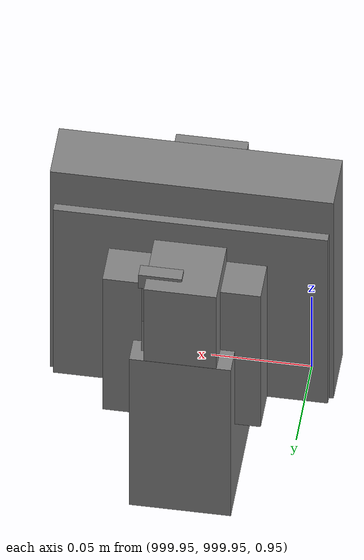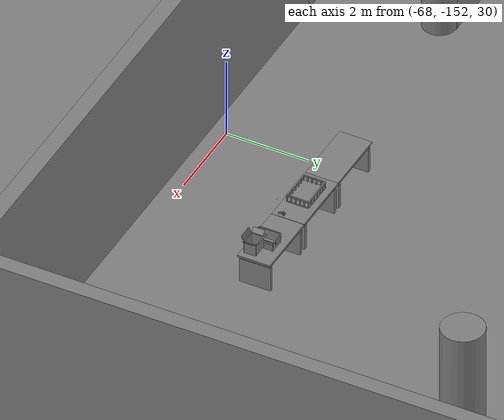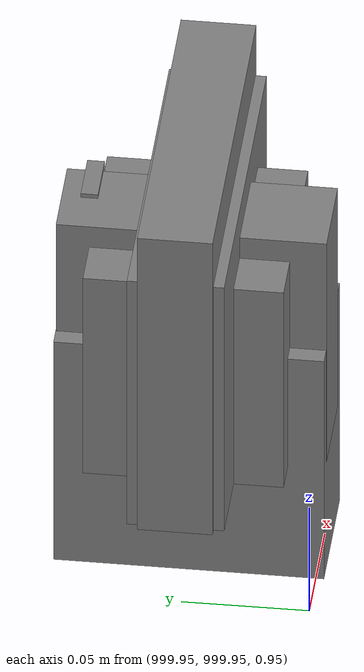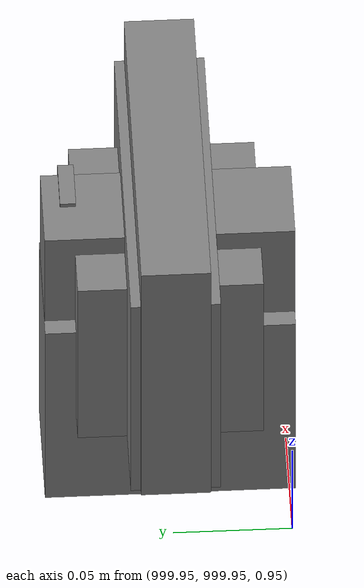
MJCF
<mujoco>
    <option gravity="0.000000000 0.000000000 -9.810000420" timestep="0.0049999999" integrator="implicitfast" density="1.225" viscosity="1.8000001e-05" noslip_iterations="10" iterations="100" sdf_iterations="50">
        <flag multiccd="disable"/>
    </option>
    <size memory="1000M"/>
    <compiler coordinate="local"/>
    <worldbody>
        <light cutoff="30" pos="0 1 1" dir="0 -1 -2"/>
        <light cutoff="30" pos="0 -1 1" dir="0 1 -2"/>
        <body pos="1000.000000000 1000.000000000 1.000000000" euler="0.000000000 0.000000000 180.000000000" name="openloong_gripper_2f85_fix_base_usda_cpu_fan">
            <geom contype="1" conaffinity="1" density="1000" type="box" material="" rgba="0.500000000 0.500000000 0.500000000 1.000000000" solimp="0.899999976 0.949999988 0.001000000" friction="1.000000000 0.005000000 0.000100000" solref="0.020000000 1.000000000" margin="0" condim="3" group="0" pos="0.000000000 0.000000000 0.070034981" quat="0.000000000 0.000000000 0.000000000 1.000000000" size="0.070700005 0.014699999 0.070700005" name="openloong_gripper_2f85_fix_base_usda_geom_01C7A971_3E69_4FA0_B86C_3ABA2D0FC8FD"/>
            <freejoint name="openloong_gripper_2f85_fix_base_usda_cpu_fan_joint"/>
            <site size="0.005000000 0.005000000 0.005000000" rgba="0.500000000 0.500000000 0.500000000 1.000000000" pos="0.000000000 0.000000000 0.000000000" quat="0.999961913 0.008726535 0.000000000 0.000000000" group="0" type="sphere" name="openloong_gripper_2f85_fix_base_usda_cpu_fancsite"/>
        </body>
        <body pos="1000.000000000 1000.000000000 1.000000000" euler="0.000000000 0.000000000 180.000000000" name="openloong_gripper_2f85_fix_base_usda_wifi_box">
            <geom contype="1" conaffinity="1" density="1000" type="box" material="" rgba="0.500000000 0.500000000 0.500000000 1.000000000" solimp="0.899999976 0.949999988 0.001000000" friction="1.000000000 0.005000000 0.000100000" solref="0.020000000 1.000000000" margin="0" condim="3" group="0" pos="0.000000000 0.000000000 0.058978677" quat="0.000000000 0.000000047 0.000000000 1.000000000" size="0.068499997 0.018999999 0.059000000" name="openloong_gripper_2f85_fix_base_usda_geom_0449B08D_1A7B_4B37_81FC_746B5A7B2548"/>
            <freejoint name="openloong_gripper_2f85_fix_base_usda_wifi_box_joint"/>
            <site size="0.005000000 0.005000000 0.005000000" rgba="0.500000000 0.500000000 0.500000000 1.000000000" pos="0.000000000 0.000000000 0.000000000" quat="0.999961913 0.008726500 0.000000000 0.000000000" group="0" type="sphere" name="openloong_gripper_2f85_fix_base_usda_wifi_boxsite"/>
        </body>
        <body pos="1000.000000000 1000.000000000 1.000000000" euler="0.000011953 0.000005123 -179.999984741" name="openloong_gripper_2f85_fix_base_usda_intel_box">
            <geom contype="1" conaffinity="1" density="1000" type="box" material="" rgba="0.500000000 0.500000000 0.500000000 1.000000000" solimp="0.899999976 0.949999988 0.001000000" friction="1.000000000 0.005000000 0.000100000" solref="0.020000000 1.000000000" margin="0" condim="3" group="0" pos="0.000000000 -0.000067139 0.000082284" quat="0.707106709 0.000000225 0.000000253 0.707106650" size="0.052800003 0.025300000 0.052800003" name="openloong_gripper_2f85_fix_base_usda_geom_BCB35E1C_A3BA_4B16_BDBF_DFB9EA45F47E"/>
            <freejoint name="openloong_gripper_2f85_fix_base_usda_intel_box_joint"/>
            <site size="0.005000000 0.005000000 0.005000000" rgba="0.500000000 0.500000000 0.500000000 1.000000000" pos="0.000000000 0.000000000 0.000000000" quat="0.999961913 0.008726500 0.000000000 0.000000000" group="0" type="sphere" name="openloong_gripper_2f85_fix_base_usda_intel_boxsite"/>
        </body>
        <body pos="-65.810035706 -149.658538818 31.165296555" euler="176.927078247 54.246105194 -44.888114929" mocap="true" name="spotlight1_SpotLight"/>
        <body pos="-66.042388916 -149.071014404 31.167587280" euler="-73.577835083 -82.027565002 49.170898438" mocap="true" name="spotlight3_SpotLight"/>
        <body pos="1000.000000000 999.999938965 1.000000000" euler="0.000000000 0.000000000 180.000000000" name="openloong_gripper_2f85_fix_base_usda_intelcore_i5">
            <geom contype="1" conaffinity="1" density="1000" type="box" material="" rgba="0.500000000 0.500000000 0.500000000 1.000000000" solimp="0.899999976 0.949999988 0.001000000" friction="1.000000000 0.005000000 0.000100000" solref="0.020000000 1.000000000" margin="0" condim="3" group="0" pos="0.000000000 0.000000000 0.051722717" quat="0.707106709 0.000000000 0.000000000 -0.707106769" size="0.052800000 0.018080002 0.052800000" name="openloong_gripper_2f85_fix_base_usda_geom_FC82C8D0_EE9B_4E37_8AE2_1E529745518C"/>
            <freejoint name="openloong_gripper_2f85_fix_base_usda_intelcore_i5_joint"/>
            <site size="0.005000000 0.005000000 0.005000000" rgba="0.500000000 0.500000000 0.500000000 1.000000000" pos="0.000000000 0.000000000 0.000000000" quat="0.999961913 0.008726534 0.000000000 0.000000000" group="0" type="sphere" name="openloong_gripper_2f85_fix_base_usda_intelcore_i5site"/>
        </body>
        <body pos="1000.000000000 1000.000000000 1.000000000" euler="0.000000000 0.000000000 180.000000000" name="openloong_gripper_2f85_fix_base_usda_battery_01">
            <geom contype="1" conaffinity="1" density="1000" type="box" material="" rgba="0.500000000 0.500000000 0.500000000 1.000000000" solimp="0.899999976 0.949999988 0.001000000" friction="1.000000000 0.005000000 0.000100000" solref="0.020000000 1.000000000" margin="0" condim="3" group="0" pos="-0.011123657 -0.041940309 0.101691343" quat="1.000000000 0.000000000 0.000000000 0.000000000" size="0.010800000 0.003375000 0.004725000" name="openloong_gripper_2f85_fix_base_usda_geom_A40114E9_A55F_4E02_B132_8265AF6C5FC1"/>
            <geom contype="1" conaffinity="1" density="1000" type="box" material="" rgba="0.500000000 0.500000000 0.500000000 1.000000000" solimp="0.899999976 0.949999988 0.001000000" friction="1.000000000 0.005000000 0.000100000" solref="0.020000000 1.000000000" margin="0" condim="3" group="0" pos="-0.010876465 -0.044247437 0.047066893" quat="0.998702705 -0.050920475 0.000000000 0.000000000" size="0.009450001 0.002700000 0.024975000" name="openloong_gripper_2f85_fix_base_usda_geom_3C850785_BFCF_4AB8_AC2E_7E84BC7E476D"/>
            <geom contype="1" conaffinity="1" density="1000" type="box" material="" rgba="0.500000000 0.500000000 0.500000000 1.000000000" solimp="0.899999976 0.949999988 0.001000000" friction="1.000000000 0.005000000 0.000100000" solref="0.020000000 1.000000000" margin="0" condim="3" group="0" pos="-0.001235962 -0.000659180 0.047381196" quat="1.000000000 0.000000000 0.000000000 0.000000000" size="0.039420001 0.039150000 0.047250003" name="openloong_gripper_2f85_fix_base_usda_geom_A31AB564_6096_43CC_95F2_80989789A2B5"/>
            <geom contype="1" conaffinity="1" density="1000" type="box" material="" rgba="0.500000000 0.500000000 0.500000000 1.000000000" solimp="0.899999976 0.949999988 0.001000000" friction="1.000000000 0.005000000 0.000100000" solref="0.020000000 1.000000000" margin="0" condim="3" group="0" pos="-0.010876465 -0.039138794 0.009851727" quat="1.000000000 0.000000000 0.000000000 0.000000000" size="0.009450001 0.010800000 0.013500000" name="openloong_gripper_2f85_fix_base_usda_geom_B4EDF551_01C6_4754_BFF3_C41AC84D94A1"/>
            <geom contype="1" conaffinity="1" density="1000" type="box" material="" rgba="0.500000000 0.500000000 0.500000000 1.000000000" solimp="0.899999976 0.949999988 0.001000000" friction="1.000000000 0.005000000 0.000100000" solref="0.020000000 1.000000000" margin="0" condim="3" group="0" pos="-0.010876465 -0.041528322 0.071508206" quat="1.000000000 0.000000000 0.000000000 0.000000000" size="0.009450001 0.002700000 0.027000001" name="openloong_gripper_2f85_fix_base_usda_geom_F722A124_C147_4E0D_81C7_CF5B10DE9596"/>
            <freejoint name="openloong_gripper_2f85_fix_base_usda_battery_01_joint"/>
            <site size="0.005000000 0.005000000 0.005000000" rgba="0.500000000 0.500000000 0.500000000 1.000000000" pos="0.000000000 0.000000000 0.000000000" quat="0.999961913 0.008726500 0.000000000 0.000000000" group="0" type="sphere" name="openloong_gripper_2f85_fix_base_usda_battery_01site"/>
        </body>
        <body pos="-65.837226868 -149.464965820 31.164068222" euler="-151.639236450 33.345478058 59.675979614" mocap="true" name="spotlight4_SpotLight"/>
        <body pos="-64.866622925 -149.383972168 30.183746338" euler="89.999984741 89.999946594 0.000000000" name="openloong_gripper_2f85_fix_base_usda_bluebox_01">
            <geom contype="1" conaffinity="1" density="1000" type="box" material="" rgba="0.500000000 0.500000000 0.500000000 1.000000000" solimp="0.899999976 0.949999988 0.001000000" friction="1.000000000 0.005000000 0.000100000" solref="0.020000000 1.000000000" margin="0" condim="3" group="0" pos="0.276580811 0.187225342 0.000068665" quat="0.707106948 0.000077471 0.707106352 0.000077486" size="0.100000001 0.057999998 0.010000000" name="openloong_gripper_2f85_fix_base_usda_geom_66A9E476_5309_42F0_A61B_35DADE43569E"/>
            <geom contype="1" conaffinity="1" density="1000" type="box" material="" rgba="0.500000000 0.500000000 0.500000000 1.000000000" solimp="0.899999976 0.949999988 0.001000000" friction="1.000000000 0.005000000 0.000100000" solref="0.020000000 1.000000000" margin="0" condim="3" group="0" pos="0.000000000 0.002883911 0.000000000" quat="0.999999881 0.000000000 0.000000000 0.000000000" size="0.254000008 0.003000000 0.172000006" name="openloong_gripper_2f85_fix_base_usda_geom_9A7C1DCE_6B2D_4AEA_8913_4250338C57A3"/>
            <geom contype="1" conaffinity="1" density="1000" type="box" material="" rgba="0.500000000 0.500000000 0.500000000 1.000000000" solimp="0.899999976 0.949999988 0.001000000" friction="1.000000000 0.005000000 0.000100000" solref="0.020000000 1.000000000" margin="0" condim="3" group="0" pos="0.000000000 0.124874115 0.173484802" quat="0.999796331 0.020176515 -0.000000015 0.000000030" size="0.259999990 0.119999997 0.007000000" name="openloong_gripper_2f85_fix_base_usda_geom_8BEC0083_5CD7_48FD_8092_71C5CA720A4B"/>
            <geom contype="1" conaffinity="1" density="1000" type="box" material="" rgba="0.500000000 0.500000000 0.500000000 1.000000000" solimp="0.899999976 0.949999988 0.001000000" friction="1.000000000 0.005000000 0.000100000" solref="0.020000000 1.000000000" margin="0" condim="3" group="0" pos="0.000000000 0.124874115 -0.173469543" quat="0.999796331 -0.020176545 -0.000000015 0.000000000" size="0.259999990 0.119999997 0.007000000" name="openloong_gripper_2f85_fix_base_usda_geom_D11D3EC9_D007_4E6A_99AA_BF2015E1A376"/>
            <geom contype="1" conaffinity="1" density="1000" type="box" material="" rgba="0.500000000 0.500000000 0.500000000 1.000000000" solimp="0.899999976 0.949999988 0.001000000" friction="1.000000000 0.005000000 0.000100000" solref="0.020000000 1.000000000" margin="0" condim="3" group="0" pos="0.000000000 0.214008331 0.188980103" quat="0.999912977 0.013176724 0.000000015 0.000000000" size="0.259999990 0.029999999 0.012500000" name="openloong_gripper_2f85_fix_base_usda_geom_0199AC4D_C832_40B9_B95D_948FE63F5D8C"/>
            <geom contype="1" conaffinity="1" density="1000" type="box" material="" rgba="0.500000000 0.500000000 0.500000000 1.000000000" solimp="0.899999976 0.949999988 0.001000000" friction="1.000000000 0.005000000 0.000100000" solref="0.020000000 1.000000000" margin="0" condim="3" group="0" pos="-0.258361816 0.125289917 0.001876831" quat="0.702796936 -0.020792112 0.710783124 0.020769298" size="0.189999998 0.119999997 0.009000000" name="openloong_gripper_2f85_fix_base_usda_geom_2EA4E8C0_8AD1_4353_A223_F05D59ACDCB8"/>
            <geom contype="1" conaffinity="1" density="1000" type="box" material="" rgba="0.500000000 0.500000000 0.500000000 1.000000000" solimp="0.899999976 0.949999988 0.001000000" friction="1.000000000 0.005000000 0.000100000" solref="0.020000000 1.000000000" margin="0" condim="3" group="0" pos="0.000000000 0.214008331 -0.188980103" quat="0.999912977 -0.013176769 0.000000030 0.000000015" size="0.259999990 0.029999999 0.012500000" name="openloong_gripper_2f85_fix_base_usda_geom_539FFEBC_272E_4700_A9D4_058305F38772"/>
            <geom contype="1" conaffinity="1" density="1000" type="box" material="" rgba="0.500000000 0.500000000 0.500000000 1.000000000" solimp="0.899999976 0.949999988 0.001000000" friction="1.000000000 0.005000000 0.000100000" solref="0.020000000 1.000000000" margin="0" condim="3" group="0" pos="-0.276611328 0.187225342 0.000068665" quat="0.707106650 0.000077441 0.707106709 0.000077456" size="0.100000001 0.057999998 0.010000000" name="openloong_gripper_2f85_fix_base_usda_geom_C9D21A64_AA5D_4F76_B3FD_125316A59DB5"/>
            <geom contype="1" conaffinity="1" density="1000" type="box" material="" rgba="0.500000000 0.500000000 0.500000000 1.000000000" solimp="0.899999976 0.949999988 0.001000000" friction="1.000000000 0.005000000 0.000100000" solref="0.020000000 1.000000000" margin="0" condim="3" group="0" pos="0.258331299 0.125289917 0.001876831" quat="0.702851415 0.018856421 0.710823774 -0.019329369" size="0.189999998 0.119999997 0.009000000" name="openloong_gripper_2f85_fix_base_usda_geom_7D619087_2AD5_4559_BADB_39DE95308864"/>
            <freejoint name="openloong_gripper_2f85_fix_base_usda_bluebox_01_joint"/>
            <site size="0.005000000 0.005000000 0.005000000" rgba="0.500000000 0.500000000 0.500000000 1.000000000" pos="0.000000000 0.000000000 0.000000000" quat="0.999961913 0.008726534 0.000000000 0.000000000" group="0" type="sphere" name="openloong_gripper_2f85_fix_base_usda_bluebox_01site"/>
        </body>
        <body pos="-64.496299744 -149.491867065 30.235729218" euler="0.000000000 0.000000000 89.999946594" name="openloong_gripper_2f85_fix_base_usda_cardboardbox_01">
            <geom contype="1" conaffinity="1" density="1000" type="box" material="" rgba="0.500000000 0.500000000 0.500000000 1.000000000" solimp="0.899999976 0.949999988 0.001000000" friction="1.000000000 0.005000000 0.000100000" solref="0.020000000 1.000000000" margin="0" condim="3" group="0" pos="-0.003166199 -0.004086494 0.005052090" quat="1.000000000 0.000000000 0.000000000 0.000000000" size="0.142499998 0.177500010 0.005000000" name="openloong_gripper_2f85_fix_base_usda_geom_047057F4_8C70_43FF_944C_08266D7384BF"/>
            <geom contype="1" conaffinity="1" density="1000" type="box" material="" rgba="0.500000000 0.500000000 0.500000000 1.000000000" solimp="0.899999976 0.949999988 0.001000000" friction="1.000000000 0.005000000 0.000100000" solref="0.020000000 1.000000000" margin="0" condim="3" group="0" pos="-0.003166199 0.170316696 0.150570869" quat="1.000000000 0.000000000 0.000000000 0.000000000" size="0.142499998 0.005000000 0.149999991" name="openloong_gripper_2f85_fix_base_usda_geom_42A225AF_A7C0_4CFE_8460_715586727AA2"/>
            <geom contype="1" conaffinity="1" density="1000" type="box" material="" rgba="0.500000000 0.500000000 0.500000000 1.000000000" solimp="0.899999976 0.949999988 0.001000000" friction="1.000000000 0.005000000 0.000100000" solref="0.020000000 1.000000000" margin="0" condim="3" group="0" pos="-0.147399902 -0.005307198 0.150570869" quat="1.000000000 0.000000000 0.000000000 0.000000000" size="0.005000000 0.177500010 0.149999991" name="openloong_gripper_2f85_fix_base_usda_geom_CFA590C7_6710_4006_B929_05A8E573343B"/>
            <geom contype="1" conaffinity="1" density="1000" type="box" material="" rgba="0.500000000 0.500000000 0.500000000 1.000000000" solimp="0.899999976 0.949999988 0.001000000" friction="1.000000000 0.005000000 0.000100000" solref="0.020000000 1.000000000" margin="0" condim="3" group="0" pos="0.140275955 -0.005307198 0.150570869" quat="1.000000000 0.000000000 0.000000000 0.000000000" size="0.005000000 0.177500010 0.149999991" name="openloong_gripper_2f85_fix_base_usda_geom_A01CA525_BDE9_42F2_9C14_E576C090C23A"/>
            <geom contype="1" conaffinity="1" density="1000" type="box" material="" rgba="0.500000000 0.500000000 0.500000000 1.000000000" solimp="0.899999976 0.949999988 0.001000000" friction="1.000000000 0.005000000 0.000100000" solref="0.020000000 1.000000000" margin="0" condim="3" group="0" pos="-0.003166199 -0.181550980 0.150570869" quat="1.000000000 0.000000000 0.000000000 0.000000000" size="0.142499998 0.005000000 0.149999991" name="openloong_gripper_2f85_fix_base_usda_geom_72A718A1_AAEA_43EB_BF75_BBC8216269AF"/>
            <freejoint name="openloong_gripper_2f85_fix_base_usda_cardboardbox_01_joint"/>
            <site size="0.005000000 0.005000000 0.005000000" rgba="0.500000000 0.500000000 0.500000000 1.000000000" pos="0.000000000 0.000000000 0.000000000" quat="0.999961913 0.008726535 0.000000000 0.000000000" group="0" type="sphere" name="openloong_gripper_2f85_fix_base_usda_site_B5B50DEB_F097_4DF0_8622_2C53CCE36C74"/>
            <body pos="0.139160156 -0.004048347 0.301930904" euler="-179.999954224 49.383502960 179.999954224" name="openloong_gripper_2f85_fix_base_usda_A1_006">
                <geom contype="1" conaffinity="1" density="1000" type="box" material="" rgba="0.500000000 0.500000000 0.500000000 1.000000000" solimp="0.899999976 0.949999988 0.001000000" friction="1.000000000 0.005000000 0.000100000" solref="0.020000000 1.000000000" margin="0" condim="3" group="0" pos="-0.071587563 0.000009537 0.001745224" quat="0.999999881 0.000000000 0.000000000 0.000000000" size="0.071249999 0.179999992 0.002500000" name="openloong_gripper_2f85_fix_base_usda_geom_74B326DC_3376_43EC_9507_9142208F0BA4"/>
                <joint armature="0" stiffness="0.07" damping="0.0099999998" axis="0.000000 1.000000 0.000000" type="hinge" name="openloong_gripper_2f85_fix_base_usda_A1_006"/>
            </body>
            <body pos="-0.145902634 -0.004086494 0.301938057" euler="-180.000000000 -60.000011444 -180.000000000" name="openloong_gripper_2f85_fix_base_usda_A2_006">
                <geom contype="1" conaffinity="1" density="1000" type="box" material="" rgba="0.500000000 0.500000000 0.500000000 1.000000000" solimp="0.899999976 0.949999988 0.001000000" friction="1.000000000 0.005000000 0.000100000" solref="0.020000000 1.000000000" margin="0" condim="3" group="0" pos="0.071268082 0.000009537 0.002717972" quat="0.000002921 0.000000000 -0.000000030 0.999999881" size="0.071249999 0.179999992 0.002500000" name="openloong_gripper_2f85_fix_base_usda_geom_8F29D6BC_6ADE_495E_B40D_096A1E5CF7EA"/>
                <joint armature="0" stiffness="0.07" damping="0.0099999998" axis="0.000000 1.000000 0.000000" type="hinge" name="openloong_gripper_2f85_fix_base_usda_A2_006"/>
            </body>
            <body pos="-0.003385544 0.175991058 0.301930904" euler="-125.858116150 -0.000004561 0.000002331" name="openloong_gripper_2f85_fix_base_usda_B2_006">
                <geom contype="1" conaffinity="1" density="1000" type="box" material="" rgba="0.500000000 0.500000000 0.500000000 1.000000000" solimp="0.899999976 0.949999988 0.001000000" friction="1.000000000 0.005000000 0.000100000" solref="0.020000000 1.000000000" margin="0" condim="3" group="0" pos="0.000009537 -0.070939064 -0.002470016" quat="0.999614120 0.027776197 -0.000000015 0.000000030" size="0.137500003 0.064999998 0.005000000" name="openloong_gripper_2f85_fix_base_usda_geom_B4FECA96_E180_4231_A1C1_B638F7EF8012"/>
                <joint armature="0" stiffness="0.07" damping="0.0099999998" axis="1.000000 0.000000 0.000000" type="hinge" name="openloong_gripper_2f85_fix_base_usda_B2_006"/>
            </body>
            <body pos="-0.003385544 -0.184140205 0.301938057" euler="147.805557251 0.000000000 0.000000000" name="openloong_gripper_2f85_fix_base_usda_B1_006">
                <geom contype="1" conaffinity="1" density="1000" type="box" material="" rgba="0.500000000 0.500000000 0.500000000 1.000000000" solimp="0.899999976 0.949999988 0.001000000" friction="1.000000000 0.005000000 0.000100000" solref="0.020000000 1.000000000" margin="0" condim="3" group="0" pos="-0.000028610 0.070202351 -0.002703667" quat="0.999614179 -0.027776167 0.000000000 0.000000000" size="0.137500003 0.064999998 0.005000000" name="openloong_gripper_2f85_fix_base_usda_geom_BE6293F5_7699_4124_B4C5_4F52AC7CAEE1"/>
                <joint armature="0" stiffness="0.07" damping="0.0099999998" axis="1.000000 0.000000 0.000000" type="hinge" name="openloong_gripper_2f85_fix_base_usda_B1_006"/>
            </body>
        </body>
        <body pos="-65.882858276 -149.481979370 30.229999542" euler="-64.487716675 0.000000000 0.000000000" name="openloong_gripper_2f85_fix_base_usda_Barcode">
            <geom contype="1" conaffinity="1" density="1000" type="box" material="" rgba="0.500000000 0.500000000 0.500000000 1.000000000" solimp="0.899999976 0.949999988 0.001000000" friction="1.000000000 0.005000000 0.000100000" solref="0.020000000 1.000000000" margin="0" condim="3" group="0" pos="0.000000000 0.013038635 0.001419067" quat="0.000000000 0.000000000 0.000000000 1.000000119" size="0.034000002 0.010000000 0.017999999" name="openloong_gripper_2f85_fix_base_usda_geom_2A3D0EB5_CC30_4B1F_B09B_5C3C7E11DBFC"/>
            <geom contype="1" conaffinity="1" density="1000" type="box" material="" rgba="0.500000000 0.500000000 0.500000000 1.000000000" solimp="0.899999976 0.949999988 0.001000000" friction="1.000000000 0.005000000 0.000100000" solref="0.020000000 1.000000000" margin="0" condim="3" group="0" pos="0.000000000 -0.035301208 -0.007095337" quat="0.000000000 0.000000000 -0.043619365 0.999048233" size="0.028999999 0.010000000 0.020000000" name="openloong_gripper_2f85_fix_base_usda_geom_4C83C26A_6139_4583_AB90_BF7096662EBC"/>
            <geom contype="1" conaffinity="1" density="1000" type="box" material="" rgba="0.500000000 0.500000000 0.500000000 1.000000000" solimp="0.899999976 0.949999988 0.001000000" friction="1.000000000 0.005000000 0.000100000" solref="0.020000000 1.000000000" margin="0" condim="3" group="0" pos="0.000000000 -0.043411255 -0.011749268" quat="0.922262907 0.386563420 0.000000000 0.000000000" size="0.026000001 0.010000000 0.020000000" name="openloong_gripper_2f85_fix_base_usda_geom_0BBB614D_2A9F_4276_A91D_F139734E5F4F"/>
            <geom contype="1" conaffinity="1" density="1000" type="box" material="" rgba="0.500000000 0.500000000 0.500000000 1.000000000" solimp="0.899999976 0.949999988 0.001000000" friction="1.000000000 0.005000000 0.000100000" solref="0.020000000 1.000000000" margin="0" condim="3" group="0" pos="0.000000000 -0.016967773 -0.031860352" quat="0.000000000 0.000000000 0.000000000 1.000000119" size="0.008000000 0.010000000 0.013000000" name="openloong_gripper_2f85_fix_base_usda_geom_AFB86F3D_4EE4_42F8_846F_B8362139DA61"/>
            <geom contype="1" conaffinity="1" density="1000" type="box" material="" rgba="0.500000000 0.500000000 0.500000000 1.000000000" solimp="0.899999976 0.949999988 0.001000000" friction="1.000000000 0.005000000 0.000100000" solref="0.020000000 1.000000000" margin="0" condim="3" group="0" pos="0.000000000 -0.001869202 0.000312805" quat="0.953716993 0.300705761 0.000000000 0.000000000" size="0.032000002 0.010000000 0.018999999" name="openloong_gripper_2f85_fix_base_usda_geom_4A05FF20_5C1F_4366_9199_2B91B98FEC33"/>
            <geom contype="1" conaffinity="1" density="1000" type="box" material="" rgba="0.500000000 0.500000000 0.500000000 1.000000000" solimp="0.899999976 0.949999988 0.001000000" friction="1.000000000 0.005000000 0.000100000" solref="0.020000000 1.000000000" margin="0" condim="3" group="0" pos="0.000000000 -0.019531250 -0.003173828" quat="0.953716993 0.300705761 0.000000000 0.000000000" size="0.030999999 0.010000000 0.020000000" name="openloong_gripper_2f85_fix_base_usda_geom_261B94F7_9514_461E_8621_970A39551BE1"/>
            <geom contype="1" conaffinity="1" density="1000" type="box" material="" rgba="0.500000000 0.500000000 0.500000000 1.000000000" solimp="0.899999976 0.949999988 0.001000000" friction="1.000000000 0.005000000 0.000100000" solref="0.020000000 1.000000000" margin="0" condim="3" group="0" pos="0.000000000 -0.035301208 -0.007095337" quat="0.953716993 0.300705761 0.000000000 0.000000000" size="0.028999999 0.010000000 0.020000000" name="openloong_gripper_2f85_fix_base_usda_geom_406E247B_F639_4A72_A5C6_4EC586CCAB53"/>
            <geom contype="1" conaffinity="1" density="1000" type="box" material="" rgba="0.500000000 0.500000000 0.500000000 1.000000000" solimp="0.899999976 0.949999988 0.001000000" friction="1.000000000 0.005000000 0.000100000" solref="0.020000000 1.000000000" margin="0" condim="3" group="0" pos="0.000000000 -0.042617798 -0.071121216" quat="0.000000000 0.000000000 0.000000000 1.000000119" size="0.013000000 0.021000000 0.059999999" name="openloong_gripper_2f85_fix_base_usda_geom_52869870_FDA1_4D13_9E9E_E5776FE733FE"/>
            <freejoint name="openloong_gripper_2f85_fix_base_usda_Barcode_joint"/>
            <site size="0.005000000 0.005000000 0.005000000" rgba="0.500000000 0.500000000 0.500000000 1.000000000" pos="0.000000000 0.000000000 0.000000000" quat="1.000000000 0.000000000 0.000000000 0.000000000" group="0" type="sphere" name="openloong_gripper_2f85_fix_base_usda_Barcode_site"/>
        </body>
        <body pos="-66.745018005 -149.392349243 30.184000015" euler="0.000000000 0.000000000 89.999946594" name="[22330760801851]_Basket_01">
            <geom contype="1" conaffinity="1" density="1000" type="box" material="" rgba="0.500000000 0.500000000 0.500000000 1.000000000" solimp="0.899999976 0.949999988 0.001000000" friction="1.000000000 0.005000000 0.000100000" solref="0.020000000 1.000000000" margin="0" condim="3" group="0" pos="-0.052425385 0.389207840 0.089787483" quat="0.707107008 0.000000000 0.000000000 0.707106411" size="0.014249999 0.014249999 0.059999999" name="[22330760801851]_geom_DEF75851_16C8_4B8A_B899_C475DEF04830"/>
            <geom contype="1" conaffinity="1" density="1000" type="box" material="" rgba="0.500000000 0.500000000 0.500000000 1.000000000" solimp="0.899999976 0.949999988 0.001000000" friction="1.000000000 0.005000000 0.000100000" solref="0.020000000 1.000000000" margin="0" condim="3" group="0" pos="0.264015198 -0.133043289 0.089787483" quat="0.707107008 0.000000000 0.000000000 0.707106411" size="0.014249999 0.014249999 0.059999999" name="[22330760801851]_geom_42BEAE2D_17D4_4055_B397_DC5CA48FDC0D"/>
            <geom contype="1" conaffinity="1" density="1000" type="box" material="" rgba="0.500000000 0.500000000 0.500000000 1.000000000" solimp="0.899999976 0.949999988 0.001000000" friction="1.000000000 0.005000000 0.000100000" solref="0.020000000 1.000000000" margin="0" condim="3" group="0" pos="-0.264015198 -0.265548706 0.089793205" quat="0.707107008 0.000000000 0.000000000 0.707106411" size="0.014249999 0.014249999 0.059999999" name="[22330760801851]_geom_433E32B9_2520_443A_A5D9_653CEF007CD0"/>
            <geom contype="1" conaffinity="1" density="1000" type="box" material="" rgba="0.500000000 0.500000000 0.500000000 1.000000000" solimp="0.899999976 0.949999988 0.001000000" friction="1.000000000 0.005000000 0.000100000" solref="0.020000000 1.000000000" margin="0" condim="3" group="0" pos="-0.160263062 -0.389322281 0.089793205" quat="0.707107008 0.000000000 0.000000000 0.707106411" size="0.014249999 0.014249999 0.059999999" name="[22330760801851]_geom_A8917001_BFFB_4ADD_B9EA_A9F48FB53E3F"/>
            <geom contype="1" conaffinity="1" density="1000" type="box" material="" rgba="0.500000000 0.500000000 0.500000000 1.000000000" solimp="0.899999976 0.949999988 0.001000000" friction="1.000000000 0.005000000 0.000100000" solref="0.020000000 1.000000000" margin="0" condim="3" group="0" pos="0.162265778 -0.389322281 0.089787483" quat="0.707107008 0.000000000 0.000000000 0.707106411" size="0.014249999 0.014249999 0.059999999" name="[22330760801851]_geom_7929BE0D_09AB_410E_86F9_40031EADB975"/>
            <geom contype="1" conaffinity="1" density="1000" type="box" material="" rgba="0.500000000 0.500000000 0.500000000 1.000000000" solimp="0.899999976 0.949999988 0.001000000" friction="1.000000000 0.005000000 0.000100000" solref="0.020000000 1.000000000" margin="0" condim="3" group="0" pos="0.264015198 0.389207840 0.089787483" quat="0.707107008 0.000000000 0.000000000 0.707106411" size="0.014249999 0.014249999 0.059999999" name="[22330760801851]_geom_A8E32B07_F910_4561_A578_946F0DBB1370"/>
            <geom contype="1" conaffinity="1" density="1000" type="box" material="" rgba="0.500000000 0.500000000 0.500000000 1.000000000" solimp="0.899999976 0.949999988 0.001000000" friction="1.000000000 0.005000000 0.000100000" solref="0.020000000 1.000000000" margin="0" condim="3" group="0" pos="-0.264015198 -0.133043289 0.089793205" quat="0.707107008 0.000000000 0.000000000 0.707106411" size="0.014249999 0.014249999 0.059999999" name="[22330760801851]_geom_A9C40ED4_18FF_4E1E_A30F_247EA04CD145"/>
            <geom contype="1" conaffinity="1" density="1000" type="box" material="" rgba="0.500000000 0.500000000 0.500000000 1.000000000" solimp="0.899999976 0.949999988 0.001000000" friction="1.000000000 0.005000000 0.000100000" solref="0.020000000 1.000000000" margin="0" condim="3" group="0" pos="-0.264026642 0.269256592 0.089793205" quat="0.707107008 0.000000000 0.000000000 0.707106411" size="0.014249999 0.014249999 0.059999999" name="[22330760801851]_geom_38F913A4_EA06_41FD_9D5C_4CAAD35BA896"/>
            <geom contype="1" conaffinity="1" density="1000" type="box" material="" rgba="0.500000000 0.500000000 0.500000000 1.000000000" solimp="0.899999976 0.949999988 0.001000000" friction="1.000000000 0.005000000 0.000100000" solref="0.020000000 1.000000000" margin="0" condim="3" group="0" pos="0.054462433 0.389207840 0.089787483" quat="0.707107008 0.000000000 0.000000000 0.707106411" size="0.014249999 0.014249999 0.059999999" name="[22330760801851]_geom_93006605_4E3D_48AE_9E53_53FE53941D27"/>
            <geom contype="1" conaffinity="1" density="1000" type="box" material="" rgba="0.500000000 0.500000000 0.500000000 1.000000000" solimp="0.899999976 0.949999988 0.001000000" friction="1.000000000 0.005000000 0.000100000" solref="0.020000000 1.000000000" margin="0" condim="3" group="0" pos="0.054462433 -0.389322281 0.089787483" quat="0.707107008 0.000000000 0.000000000 0.707106411" size="0.014249999 0.014249999 0.059999999" name="[22330760801851]_geom_DBC07288_829F_4B93_9741_E0C90AA74FCE"/>
            <geom contype="1" conaffinity="1" density="1000" type="box" material="" rgba="0.500000000 0.500000000 0.500000000 1.000000000" solimp="0.899999976 0.949999988 0.001000000" friction="1.000000000 0.005000000 0.000100000" solref="0.020000000 1.000000000" margin="0" condim="3" group="0" pos="0.264015198 0.269256592 0.089793205" quat="0.707107008 0.000000000 0.000000000 0.707106411" size="0.014249999 0.014249999 0.059999999" name="[22330760801851]_geom_62B96D73_7865_4ADE_AE80_8C21022620B6"/>
            <geom contype="1" conaffinity="1" density="1000" type="box" material="" rgba="0.500000000 0.500000000 0.500000000 1.000000000" solimp="0.899999976 0.949999988 0.001000000" friction="1.000000000 0.005000000 0.000100000" solref="0.020000000 1.000000000" margin="0" condim="3" group="0" pos="0.264015198 -0.389322281 0.089787483" quat="0.707107008 0.000000000 0.000000000 0.707106411" size="0.014249999 0.014249999 0.059999999" name="[22330760801851]_geom_2ABEDB40_E408_4F85_8F99_736F4DAB3203"/>
            <geom contype="1" conaffinity="1" density="1000" type="box" material="" rgba="0.500000000 0.500000000 0.500000000 1.000000000" solimp="0.899999976 0.949999988 0.001000000" friction="1.000000000 0.005000000 0.000100000" solref="0.020000000 1.000000000" margin="0" condim="3" group="0" pos="0.000000000 0.000000000 0.015998840" quat="0.707107008 0.000000000 0.000000000 0.707106411" size="0.403499991 0.279000014 0.015750000" name="[22330760801851]_geom_06D5499A_386C_411C_B180_2300E780008A"/>
            <geom contype="1" conaffinity="1" density="1000" type="box" material="" rgba="0.500000000 0.500000000 0.500000000 1.000000000" solimp="0.899999976 0.949999988 0.001000000" friction="1.000000000 0.005000000 0.000100000" solref="0.020000000 1.000000000" margin="0" condim="3" group="0" pos="0.000000000 -0.389476776 0.163619041" quat="0.707107008 0.000000000 0.000000000 0.707106411" size="0.015000000 0.277500004 0.015750000" name="[22330760801851]_geom_7E5ADB2A_EA84_468D_9299_472D9F3E6119"/>
            <geom contype="1" conaffinity="1" density="1000" type="box" material="" rgba="0.500000000 0.500000000 0.500000000 1.000000000" solimp="0.899999976 0.949999988 0.001000000" friction="1.000000000 0.005000000 0.000100000" solref="0.020000000 1.000000000" margin="0" condim="3" group="0" pos="0.162265778 0.389207840 0.089787483" quat="0.707107008 0.000000000 0.000000000 0.707106411" size="0.014249999 0.014249999 0.059999999" name="[22330760801851]_geom_A6F5B0B4_003A_405E_8391_452C11ECAE66"/>
            <geom contype="1" conaffinity="1" density="1000" type="box" material="" rgba="0.500000000 0.500000000 0.500000000 1.000000000" solimp="0.899999976 0.949999988 0.001000000" friction="1.000000000 0.005000000 0.000100000" solref="0.020000000 1.000000000" margin="0" condim="3" group="0" pos="0.000000000 0.389471054 0.163619041" quat="0.707107008 0.000000000 0.000000000 0.707106411" size="0.015000000 0.277500004 0.015750000" name="[22330760801851]_geom_5B0D5F46_098D_46DB_B62C_A7D7C773D740"/>
            <geom contype="1" conaffinity="1" density="1000" type="box" material="" rgba="0.500000000 0.500000000 0.500000000 1.000000000" solimp="0.899999976 0.949999988 0.001000000" friction="1.000000000 0.005000000 0.000100000" solref="0.020000000 1.000000000" margin="0" condim="3" group="0" pos="-0.263511658 0.000000000 0.163619041" quat="0.707107008 0.000000000 0.000000000 0.707106411" size="0.403499991 0.015000000 0.015750000" name="[22330760801851]_geom_A81CBCF6_9D4A_4CC6_9DE6_68659384D14C"/>
            <geom contype="1" conaffinity="1" density="1000" type="box" material="" rgba="0.500000000 0.500000000 0.500000000 1.000000000" solimp="0.899999976 0.949999988 0.001000000" friction="1.000000000 0.005000000 0.000100000" solref="0.020000000 1.000000000" margin="0" condim="3" group="0" pos="-0.264015198 0.141334534 0.089793205" quat="0.707107008 0.000000000 0.000000000 0.707106411" size="0.014249999 0.014249999 0.059999999" name="[22330760801851]_geom_C5482FE2_5043_4275_955C_6C1D94E9CBDC"/>
            <geom contype="1" conaffinity="1" density="1000" type="box" material="" rgba="0.500000000 0.500000000 0.500000000 1.000000000" solimp="0.899999976 0.949999988 0.001000000" friction="1.000000000 0.005000000 0.000100000" solref="0.020000000 1.000000000" margin="0" condim="3" group="0" pos="0.264015198 -0.265548706 0.089787483" quat="0.707107008 0.000000000 0.000000000 0.707106411" size="0.014249999 0.014249999 0.059999999" name="[22330760801851]_geom_CC616E47_CCD8_4465_9D7E_D86080F6E1E3"/>
            <geom contype="1" conaffinity="1" density="1000" type="box" material="" rgba="0.500000000 0.500000000 0.500000000 1.000000000" solimp="0.899999976 0.949999988 0.001000000" friction="1.000000000 0.005000000 0.000100000" solref="0.020000000 1.000000000" margin="0" condim="3" group="0" pos="-0.160263062 0.389207840 0.089787483" quat="0.707107008 0.000000000 0.000000000 0.707106411" size="0.014249999 0.014249999 0.059999999" name="[22330760801851]_geom_7937AF28_79FE_4C18_8BAE_BE32B89C7EC4"/>
            <geom contype="1" conaffinity="1" density="1000" type="box" material="" rgba="0.500000000 0.500000000 0.500000000 1.000000000" solimp="0.899999976 0.949999988 0.001000000" friction="1.000000000 0.005000000 0.000100000" solref="0.020000000 1.000000000" margin="0" condim="3" group="0" pos="-0.052425385 -0.389322281 0.089787483" quat="0.707107008 0.000000000 0.000000000 0.707106411" size="0.014249999 0.014249999 0.059999999" name="[22330760801851]_geom_D091BED9_A676_4A10_B1CE_167A588736AB"/>
            <geom contype="1" conaffinity="1" density="1000" type="box" material="" rgba="0.500000000 0.500000000 0.500000000 1.000000000" solimp="0.899999976 0.949999988 0.001000000" friction="1.000000000 0.005000000 0.000100000" solref="0.020000000 1.000000000" margin="0" condim="3" group="0" pos="-0.264026642 -0.389322281 0.089793205" quat="0.707107008 0.000000000 0.000000000 0.707106411" size="0.014249999 0.014249999 0.059999999" name="[22330760801851]_geom_4069067A_BB31_45C9_9C29_518BB89A57F1"/>
            <geom contype="1" conaffinity="1" density="1000" type="box" material="" rgba="0.500000000 0.500000000 0.500000000 1.000000000" solimp="0.899999976 0.949999988 0.001000000" friction="1.000000000 0.005000000 0.000100000" solref="0.020000000 1.000000000" margin="0" condim="3" group="0" pos="0.264015198 0.141334534 0.089787483" quat="0.707107008 0.000000000 0.000000000 0.707106411" size="0.014249999 0.014249999 0.059999999" name="[22330760801851]_geom_68BE6C59_68E9_4034_A80E_158FF2FC48F3"/>
            <geom contype="1" conaffinity="1" density="1000" type="box" material="" rgba="0.500000000 0.500000000 0.500000000 1.000000000" solimp="0.899999976 0.949999988 0.001000000" friction="1.000000000 0.005000000 0.000100000" solref="0.020000000 1.000000000" margin="0" condim="3" group="0" pos="-0.264015198 0.389207840 0.089793205" quat="0.707107008 0.000000000 0.000000000 0.707106411" size="0.014249999 0.014249999 0.059999999" name="[22330760801851]_geom_A60FBD3C_8C33_4B35_BB9D_BF750FF7C96F"/>
            <geom contype="1" conaffinity="1" density="1000" type="box" material="" rgba="0.500000000 0.500000000 0.500000000 1.000000000" solimp="0.899999976 0.949999988 0.001000000" friction="1.000000000 0.005000000 0.000100000" solref="0.020000000 1.000000000" margin="0" condim="3" group="0" pos="0.264015198 0.004480362 0.089787483" quat="0.707107008 0.000000000 0.000000000 0.707106411" size="0.014249999 0.014249999 0.059999999" name="[22330760801851]_geom_1EFD1D2F_4074_4902_A5DE_CD35A7E10F82"/>
            <geom contype="1" conaffinity="1" density="1000" type="box" material="" rgba="0.500000000 0.500000000 0.500000000 1.000000000" solimp="0.899999976 0.949999988 0.001000000" friction="1.000000000 0.005000000 0.000100000" solref="0.020000000 1.000000000" margin="0" condim="3" group="0" pos="0.263694763 -0.000011444 0.163619041" quat="0.707107008 0.000000000 0.000000000 0.707106411" size="0.403499991 0.015000000 0.015750000" name="[22330760801851]_geom_9E4E6D46_C942_49D6_B605_C103C08F57F2"/>
            <geom contype="1" conaffinity="1" density="1000" type="box" material="" rgba="0.500000000 0.500000000 0.500000000 1.000000000" solimp="0.899999976 0.949999988 0.001000000" friction="1.000000000 0.005000000 0.000100000" solref="0.020000000 1.000000000" margin="0" condim="3" group="0" pos="-0.264015198 0.004480362 0.089793205" quat="0.707107008 0.000000000 0.000000000 0.707106411" size="0.014249999 0.014249999 0.059999999" name="[22330760801851]_geom_4015DBB3_E153_40EF_964D_EA21577B65D1"/>
            <freejoint name="[22330760801851]_joint_AD8977BE_6CFE_40AF_B227_CF2C8F005B28"/>
        </body>
        <body pos="0.000000000 0.000000000 0.000000000" euler="0.000000000 0.000000000 0.000000000" name="Static Objects_Static Objects">
            <geom contype="1" conaffinity="1" density="1000" type="box" material="" rgba="0.500000000 0.500000000 0.500000000 1.000000000" solimp="0.899999976 0.949999988 0.001000000" friction="1.000000000 0.005000000 0.000100000" solref="0.020000000 1.000000000" margin="0" condim="3" group="0" pos="-67.544113159 -149.365814209 29.727830887" quat="0.500000417 0.499999970 0.499999553 0.499999970" size="0.381000012 0.319999993 0.041000001" name="Static Objects_geom_FDF91EA2_4F64_44D6_8FFA_9870882516D6"/>
            <geom contype="1" conaffinity="1" density="1000" type="box" material="" rgba="0.500000000 0.500000000 0.500000000 1.000000000" solimp="0.899999976 0.949999988 0.001000000" friction="1.000000000 0.005000000 0.000100000" solref="0.020000000 1.000000000" margin="0" condim="3" group="0" pos="-68.239501953 -149.365814209 30.086868286" quat="0.500000417 0.499999970 0.499999553 0.499999970" size="0.370999992 0.039500002 0.745000005" name="Static Objects_geom_73E92C77_CEAC_498B_9902_FD31A69BD414"/>
            <geom contype="1" conaffinity="1" density="1000" type="box" material="" rgba="0.500000000 0.500000000 0.500000000 1.000000000" solimp="0.899999976 0.949999988 0.001000000" friction="1.000000000 0.005000000 0.000100000" solref="0.020000000 1.000000000" margin="0" condim="3" group="0" pos="-68.239501953 -149.365814209 30.147235870" quat="0.500000417 0.499999970 0.499999553 0.499999970" size="0.400000006 0.022000000 0.800000012" name="Static Objects_geom_028B12B1_F3E5_452F_93A7_140918805CBE"/>
            <geom contype="1" conaffinity="1" density="1000" type="box" material="" rgba="0.500000000 0.500000000 0.500000000 1.000000000" solimp="0.899999976 0.949999988 0.001000000" friction="1.000000000 0.005000000 0.000100000" solref="0.020000000 1.000000000" margin="0" condim="3" group="0" pos="-68.934890747 -149.365814209 29.727830887" quat="0.500000417 0.499999970 0.499999553 0.499999970" size="0.381000012 0.319999993 0.041000001" name="Static Objects_geom_D98D69E8_9D39_4C1C_A5EA_A227C25309C6"/>
            <geom contype="1" conaffinity="1" density="1000" type="box" material="" rgba="0.500000000 0.500000000 0.500000000 1.000000000" solimp="0.899999976 0.949999988 0.001000000" friction="1.000000000 0.005000000 0.000100000" solref="0.020000000 1.000000000" margin="0" condim="3" group="0" pos="-68.239501953 -149.365814209 29.561563492" quat="0.500000417 0.499999970 0.499999553 0.499999970" size="0.020000000 0.022000000 0.660000026" name="Static Objects_geom_42C6118C_06F5_4807_AFEA_5DAAD7E7670A"/>
            <geom contype="1" conaffinity="1" density="1000" type="box" material="" rgba="0.500000000 0.500000000 0.500000000 1.000000000" solimp="0.899999976 0.949999988 0.001000000" friction="1.000000000 0.005000000 0.000100000" solref="0.020000000 1.000000000" margin="0" condim="3" group="0" pos="-65.945671082 -149.365814209 29.727830887" quat="0.500000417 0.499999970 0.499999553 0.499999970" size="0.381000012 0.319999993 0.041000001" name="Static Objects_geom_270FEC41_AD01_4D8E_878E_1647287AE1B0"/>
            <geom contype="1" conaffinity="1" density="1000" type="box" material="" rgba="0.500000000 0.500000000 0.500000000 1.000000000" solimp="0.899999976 0.949999988 0.001000000" friction="1.000000000 0.005000000 0.000100000" solref="0.020000000 1.000000000" margin="0" condim="3" group="0" pos="-66.641059875 -149.365814209 30.086868286" quat="0.500000417 0.499999970 0.499999553 0.499999970" size="0.370999992 0.039500002 0.745000005" name="Static Objects_geom_C6E0BF0B_435E_49DE_8508_546664532801"/>
            <geom contype="1" conaffinity="1" density="1000" type="box" material="" rgba="0.500000000 0.500000000 0.500000000 1.000000000" solimp="0.899999976 0.949999988 0.001000000" friction="1.000000000 0.005000000 0.000100000" solref="0.020000000 1.000000000" margin="0" condim="3" group="0" pos="-66.641059875 -149.365814209 30.147235870" quat="0.500000417 0.499999970 0.499999553 0.499999970" size="0.400000006 0.022000000 0.800000012" name="Static Objects_geom_12B3BC1A_1323_441F_99EF_8319ADE4F29F"/>
            <geom contype="1" conaffinity="1" density="1000" type="box" material="" rgba="0.500000000 0.500000000 0.500000000 1.000000000" solimp="0.899999976 0.949999988 0.001000000" friction="1.000000000 0.005000000 0.000100000" solref="0.020000000 1.000000000" margin="0" condim="3" group="0" pos="-67.336448669 -149.365814209 29.727830887" quat="0.500000417 0.499999970 0.499999553 0.499999970" size="0.381000012 0.319999993 0.041000001" name="Static Objects_geom_69BC5927_6A1A_48F7_8D57_28FCFC7821ED"/>
            <geom contype="1" conaffinity="1" density="1000" type="box" material="" rgba="0.500000000 0.500000000 0.500000000 1.000000000" solimp="0.899999976 0.949999988 0.001000000" friction="1.000000000 0.005000000 0.000100000" solref="0.020000000 1.000000000" margin="0" condim="3" group="0" pos="-66.641059875 -149.365814209 29.561563492" quat="0.500000417 0.499999970 0.499999553 0.499999970" size="0.020000000 0.022000000 0.660000026" name="Static Objects_geom_6C089E8E_FF84_4A6C_8BF1_F3AA83C0429E"/>
            <geom contype="1" conaffinity="1" density="1000" type="box" material="" rgba="0.500000000 0.500000000 0.500000000 1.000000000" solimp="0.899999976 0.949999988 0.001000000" friction="1.000000000 0.005000000 0.000100000" solref="0.020000000 1.000000000" margin="0" condim="3" group="0" pos="-64.338577271 -149.365814209 29.727830887" quat="0.500000417 0.499999970 0.499999553 0.499999970" size="0.381000012 0.319999993 0.041000001" name="Static Objects_geom_A873F385_8B5B_463F_8D74_EBC93486C73B"/>
            <geom contype="1" conaffinity="1" density="1000" type="box" material="" rgba="0.500000000 0.500000000 0.500000000 1.000000000" solimp="0.899999976 0.949999988 0.001000000" friction="1.000000000 0.005000000 0.000100000" solref="0.020000000 1.000000000" margin="0" condim="3" group="0" pos="-65.033966064 -149.365814209 30.086868286" quat="0.500000417 0.499999970 0.499999553 0.499999970" size="0.370999992 0.039500002 0.745000005" name="Static Objects_geom_7A30FA05_248B_4934_8225_33EA6C2F048E"/>
            <geom contype="1" conaffinity="1" density="1000" type="box" material="" rgba="0.500000000 0.500000000 0.500000000 1.000000000" solimp="0.899999976 0.949999988 0.001000000" friction="1.000000000 0.005000000 0.000100000" solref="0.020000000 1.000000000" margin="0" condim="3" group="0" pos="-65.033966064 -149.365814209 30.147235870" quat="0.500000417 0.499999970 0.499999553 0.499999970" size="0.400000006 0.022000000 0.800000012" name="Static Objects_geom_4DAADA9F_8649_4EE8_A664_CDECDE9D2F9B"/>
            <geom contype="1" conaffinity="1" density="1000" type="box" material="" rgba="0.500000000 0.500000000 0.500000000 1.000000000" solimp="0.899999976 0.949999988 0.001000000" friction="1.000000000 0.005000000 0.000100000" solref="0.020000000 1.000000000" margin="0" condim="3" group="0" pos="-65.729354858 -149.365814209 29.727830887" quat="0.500000417 0.499999970 0.499999553 0.499999970" size="0.381000012 0.319999993 0.041000001" name="Static Objects_geom_65D3C34F_45A0_4DAD_96CF_47AE58BCD057"/>
            <geom contype="1" conaffinity="1" density="1000" type="box" material="" rgba="0.500000000 0.500000000 0.500000000 1.000000000" solimp="0.899999976 0.949999988 0.001000000" friction="1.000000000 0.005000000 0.000100000" solref="0.020000000 1.000000000" margin="0" condim="3" group="0" pos="-65.033966064 -149.365814209 29.561563492" quat="0.500000417 0.499999970 0.499999553 0.499999970" size="0.020000000 0.022000000 0.660000026" name="Static Objects_geom_2F2EAD3C_2D3C_432C_A66A_0E188BDC7979"/>
            <geom contype="1" conaffinity="1" density="1000" type="box" material="" rgba="0.500000000 0.500000000 0.500000000 1.000000000" solimp="0.899999976 0.949999988 0.001000000" friction="1.000000000 0.005000000 0.000100000" solref="0.020000000 1.000000000" margin="0" condim="3" group="0" pos="-61.754566193 -137.853729248 33.906845093" quat="0.707107067 0.000000000 0.000000000 0.707106471" size="0.759999990 0.759999990 4.500000000" name="Static Objects_geom_27C0AB85_AB21_4711_BA38_2BCAB1A191CC"/>
            <geom contype="1" conaffinity="1" density="1000" type="box" material="" rgba="0.500000000 0.500000000 0.500000000 1.000000000" solimp="0.899999976 0.949999988 0.001000000" friction="1.000000000 0.005000000 0.000100000" solref="0.020000000 1.000000000" margin="0" condim="3" group="0" pos="-57.511135101 -144.927108765 31.707921982" quat="1.000000000 0.000000000 0.000000000 0.000000000" size="0.200000003 8.000000000 2.299999952" name="Static Objects_geom_14F632BD_B621_4751_AF23_8C2873F841FD"/>
            <geom contype="1" conaffinity="1" density="1000" type="box" material="" rgba="0.500000000 0.500000000 0.500000000 1.000000000" solimp="0.899999976 0.949999988 0.001000000" friction="1.000000000 0.005000000 0.000100000" solref="0.020000000 1.000000000" margin="0" condim="3" group="0" pos="-80.517646790 -157.574050903 31.688196182" quat="0.707107067 0.000000000 0.000000000 0.707106471" size="0.600000024 0.600000024 2.299999952" name="Static Objects_geom_D889D700_FD85_42BB_B90C_2D49A98B665E"/>
            <geom contype="1" conaffinity="1" density="1000" type="box" material="" rgba="0.500000000 0.500000000 0.500000000 1.000000000" solimp="0.899999976 0.949999988 0.001000000" friction="1.000000000 0.005000000 0.000100000" solref="0.020000000 1.000000000" margin="0" condim="3" group="0" pos="-80.711044312 -147.414932251 31.666158676" quat="1.000000000 0.000000000 0.000000000 0.000000000" size="0.200000003 10.000000000 2.299999952" name="Static Objects_geom_2518353D_75C6_446D_9561_83A08D9C972E"/>
            <geom contype="1" conaffinity="1" density="1000" type="box" material="" rgba="0.500000000 0.500000000 0.500000000 1.000000000" solimp="0.899999976 0.949999988 0.001000000" friction="1.000000000 0.005000000 0.000100000" solref="0.020000000 1.000000000" margin="0" condim="3" group="0" pos="-57.687217712 -137.434692383 31.688196182" quat="0.707107067 0.000000000 0.000000000 0.707106471" size="0.600000024 0.600000024 2.299999952" name="Static Objects_geom_267AEAC3_8EDC_4371_A538_7E38B6352595"/>
            <geom contype="1" conaffinity="1" density="1000" type="box" material="" rgba="0.500000000 0.500000000 0.500000000 1.000000000" solimp="0.899999976 0.949999988 0.001000000" friction="1.000000000 0.005000000 0.000100000" solref="0.020000000 1.000000000" margin="0" condim="3" group="0" pos="-69.537033081 -140.263229370 31.714921951" quat="0.707107067 0.000000000 0.000000000 0.707106471" size="0.759999990 4.500000000 2.299999952" name="Static Objects_geom_EA638C02_30BE_4230_8201_1475C96EEED2"/>
            <geom contype="1" conaffinity="1" density="1000" type="box" material="" rgba="0.500000000 0.500000000 0.500000000 1.000000000" solimp="0.899999976 0.949999988 0.001000000" friction="1.000000000 0.005000000 0.000100000" solref="0.020000000 1.000000000" margin="0" condim="3" group="0" pos="-80.073638916 -137.853713989 33.906845093" quat="0.707107067 0.000000000 0.000000000 0.707106471" size="0.759999990 0.759999990 4.500000000" name="Static Objects_geom_5C0F067F_2D26_4419_B457_FB7A355BC9FC"/>
            <geom contype="1" conaffinity="1" density="1000" type="box" material="" rgba="0.500000000 0.500000000 0.500000000 1.000000000" solimp="0.899999976 0.949999988 0.001000000" friction="1.000000000 0.005000000 0.000100000" solref="0.020000000 1.000000000" margin="0" condim="3" group="0" pos="-73.406707764 -155.734664917 31.707921982" quat="1.000000000 0.000000000 0.000000000 0.000000000" size="0.200000003 3.000000000 2.299999952" name="Static Objects_geom_7C992A44_8040_4209_8459_119BD77B2492"/>
            <geom contype="1" conaffinity="1" density="1000" type="box" material="" rgba="0.500000000 0.500000000 0.500000000 1.000000000" solimp="0.899999976 0.949999988 0.001000000" friction="1.000000000 0.005000000 0.000100000" solref="0.020000000 1.000000000" margin="0" condim="3" group="0" pos="-68.497543335 -137.448257446 31.707921982" quat="0.707107067 0.000000000 0.000000000 0.707106471" size="0.200000003 14.000000000 2.299999952" name="Static Objects_geom_28CF35AD_D850_4F7C_A62B_521128A761F6"/>
            <geom contype="1" conaffinity="1" density="1000" type="cylinder" material="" rgba="0.500000000 0.500000000 0.500000000 1.000000000" solimp="0.899999976 0.949999988 0.001000000" friction="1.000000000 0.005000000 0.000100000" solref="0.020000000 1.000000000" margin="0" condim="3" group="0" pos="-68.868522644 -142.134506226 31.711090088" quat="0.707107067 0.000000000 0.000000000 0.707106471" size="0.509999990 2.299999952 1.000000000" name="Static Objects_geom_13C80DC6_060C_4DDD_B557_C2826841D1A0"/>
            <geom contype="1" conaffinity="1" density="1000" type="plane" material="" rgba="0.500000000 0.500000000 0.500000000 1.000000000" solimp="0.899999976 0.949999988 0.001000000" friction="1.000000000 0.005000000 0.000100000" solref="0.020000000 1.000000000" margin="0" condim="3" group="0" pos="-72.873703003 -147.131927490 29.409669876" quat="1.000000000 0.000000000 0.000000000 0.000000000" size="18.000000000 14.000000000 1.000000000" name="Static Objects_geom_3C9F3BFF_5A0D_4F85_899A_FB6C1FDB95E6"/>
            <geom contype="1" conaffinity="1" density="1000" type="box" material="" rgba="0.500000000 0.500000000 0.500000000 1.000000000" solimp="0.899999976 0.949999988 0.001000000" friction="1.000000000 0.005000000 0.000100000" solref="0.020000000 1.000000000" margin="0" condim="3" group="0" pos="-79.943580627 -157.782272339 31.707921982" quat="0.707107067 0.000000000 0.000000000 0.707106471" size="0.200000003 7.000000000 2.299999952" name="Static Objects_geom_FCCA2751_BCB0_4B38_B528_87677FE161BC"/>
            <geom contype="1" conaffinity="1" density="1000" type="box" material="" rgba="0.500000000 0.500000000 0.500000000 1.000000000" solimp="0.899999976 0.949999988 0.001000000" friction="1.000000000 0.005000000 0.000100000" solref="0.020000000 1.000000000" margin="0" condim="3" group="0" pos="-65.421028137 -152.903442383 31.707921982" quat="0.707107067 0.000000000 0.000000000 0.707106471" size="0.200000003 7.800000191 2.299999952" name="Static Objects_geom_6C07C401_50FF_41BA_A092_0554692BB9A7"/>
            <geom contype="1" conaffinity="1" density="1000" type="box" material="" rgba="0.500000000 0.500000000 0.500000000 1.000000000" solimp="0.899999976 0.949999988 0.001000000" friction="1.000000000 0.005000000 0.000100000" solref="0.020000000 1.000000000" margin="0" condim="3" group="0" pos="-74.776908875 -149.964416504 31.688196182" quat="1.000000000 0.000000000 0.000000000 0.000000000" size="0.600000024 0.409999996 2.299999952" name="Static Objects_geom_495F4C06_CD39_497D_B118_EB8396303CAF"/>
            <geom contype="1" conaffinity="1" density="1000" type="cylinder" material="" rgba="0.500000000 0.500000000 0.500000000 1.000000000" solimp="0.899999976 0.949999988 0.001000000" friction="1.000000000 0.005000000 0.000100000" solref="0.020000000 1.000000000" margin="0" condim="3" group="0" pos="-60.161884308 -142.134506226 31.711090088" quat="0.707107067 0.000000000 0.000000000 0.707106471" size="0.509999990 2.299999952 1.000000000" name="Static Objects_geom_E296CA15_B626_48B7_AB53_5FFB40F16935"/>
            <geom contype="1" conaffinity="1" density="1000" type="cylinder" material="" rgba="0.500000000 0.500000000 0.500000000 1.000000000" solimp="0.899999976 0.949999988 0.001000000" friction="1.000000000 0.005000000 0.000100000" solref="0.020000000 1.000000000" margin="0" condim="3" group="0" pos="-75.382453918 -149.963455200 31.711090088" quat="0.707107067 0.000000000 0.000000000 0.707106471" size="0.409999996 2.299999952 1.000000000" name="Static Objects_geom_CAAE59C6_F6C1_4ECF_9DA0_796ADE0E3BF3"/>
            <geom contype="1" conaffinity="1" density="1000" type="cylinder" material="" rgba="0.500000000 0.500000000 0.500000000 1.000000000" solimp="0.899999976 0.949999988 0.001000000" friction="1.000000000 0.005000000 0.000100000" solref="0.020000000 1.000000000" margin="0" condim="3" group="0" pos="-74.154960632 -149.963455200 31.711090088" quat="0.707107067 0.000000000 0.000000000 0.707106471" size="0.409999996 2.299999952 1.000000000" name="Static Objects_geom_548125DE_6336_4CC9_B116_E8AE8F7C97E8"/>
            <geom contype="1" conaffinity="1" density="1000" type="cylinder" material="" rgba="0.500000000 0.500000000 0.500000000 1.000000000" solimp="0.899999976 0.949999988 0.001000000" friction="1.000000000 0.005000000 0.000100000" solref="0.020000000 1.000000000" margin="0" condim="3" group="0" pos="-77.566612244 -142.134506226 31.711090088" quat="0.707107067 0.000000000 0.000000000 0.707106471" size="0.509999990 2.299999952 1.000000000" name="Static Objects_geom_9CA88BEF_0D12_4A7B_86CD_5B48EF5DF215"/>
        </body>
        <body pos="-66.291030884 -149.869689941 29.018842697" euler="0.000000000 0.000000000 89.999946594" mocap="true" name="openloong_gripper_2f85_fix_base_usda_leftHandMocap"/>
        <body pos="-66.291030884 -149.869689941 29.018842697" euler="0.000000000 0.000000000 89.999946594" mocap="true" name="openloong_gripper_2f85_fix_base_usda_rightHandMocap"/>
        <body pos="-66.291030884 -149.869689941 30.218843460" euler="0.000000000 0.000000000 89.999946594" name="openloong_gripper_2f85_fix_base_usda_base_link">
            <geom contype="1" conaffinity="1" density="1000" type="mesh" material="" rgba="0.783999979 0.783999979 0.783999979 1.000000000" solimp="0.899999976 0.949999988 0.001000000" friction="1.000000000 0.005000000 0.000100000" solref="0.020000000 1.000000000" margin="0" condim="3" group="3" mesh="base_link" pos="0.000000000 0.000000000 0.000000000" quat="1.000000000 0.000000000 0.000000000 0.000000000" size="1.000000000 1.000000000 1.000000000" name="openloong_gripper_2f85_fix_base_usda__geom_7_9BDDB86D_951D_4B6F_9A2B_BC3C721872D5"/>
            <site size="0.005000000 0.005000000 0.005000000" rgba="0.500000000 0.500000000 0.500000000 1.000000000" pos="0.000000000 0.000000000 0.000000000" quat="1.000000000 0.000000000 0.000000000 0.000000000" group="0" type="sphere" name="openloong_gripper_2f85_fix_base_usda_imu"/>
            <inertial mass="22.447001" pos="-0.005664100 -0.001336700 0.238289997" diaginertia="0.374352545 0.277180195 0.220617250" quat="0.999247074 0.035235517 -0.015086859 0.006023135"/>
            <body pos="0.000000000 0.000000000 0.299997330" euler="0.000000000 0.000000000 0.000000000" name="openloong_gripper_2f85_fix_base_usda_dummy_body">
                <geom contype="1" conaffinity="1" density="1000" type="sphere" material="" rgba="0.783999979 0.783999979 0.783999979 1.000000000" solimp="0.899999976 0.949999988 0.001000000" friction="1.000000000 0.005000000 0.000100000" solref="0.020000000 1.000000000" margin="0" condim="3" group="3" pos="0.000000000 0.000000000 0.000000000" quat="1.000000000 0.000000000 0.000000000 0.000000000" size="0.010000000 0.000000000 0.000000000" name="openloong_gripper_2f85_fix_base_usda__geom_8_70054E2E_3DFD_4DAC_BC64_A5481B355D49"/>
                <joint armature="0.0099999998" stiffness="0" damping="0.1" axis="0.000000 0.000000 1.000000" type="hinge" name="openloong_gripper_2f85_fix_base_usda_dummy_joint"/>
                <site size="0.010000000 0.005000000 0.005000000" rgba="0.500000000 0.500000000 0.500000000 1.000000000" pos="0.000000000 0.000000000 0.000000000" quat="1.000000000 0.000000000 0.000000000 0.000000000" group="3" type="sphere" name="openloong_gripper_2f85_fix_base_usda_dummy_site"/>
            </body>
            <body pos="0.009002686 0.000000000 0.406400681" euler="0.000000000 0.000000000 0.000000000" name="openloong_gripper_2f85_fix_base_usda_Link_head_yaw">
                <geom contype="1" conaffinity="1" density="1000" type="mesh" material="" rgba="0.783999979 0.783999979 0.783999979 1.000000000" solimp="0.899999976 0.949999988 0.001000000" friction="1.000000000 0.005000000 0.000100000" solref="0.020000000 1.000000000" margin="0" condim="3" group="3" mesh="Link_head_yaw" pos="0.000000000 0.000000000 0.000000000" quat="1.000000000 0.000000000 0.000000000 0.000000000" size="1.000000000 1.000000000 1.000000000" name="openloong_gripper_2f85_fix_base_usda__geom_10_5BFE5D33_7861_4E25_864B_6D2289B79885"/>
                <inertial mass="0.84249002" pos="0.000000000 -0.002081400 0.044801001" diaginertia="0.000700588 0.000629000 0.000553812" quat="0.706933022 -0.015675601 0.015677100 0.706933022"/>
                <body pos="0.000000000 -0.034599304 0.048500061" euler="0.000000000 0.000000000 0.000000000" name="openloong_gripper_2f85_fix_base_usda_Link_head_pitch">
                    <geom contype="1" conaffinity="1" density="1000" type="mesh" material="" rgba="0.783999979 0.783999979 0.783999979 1.000000000" solimp="0.899999976 0.949999988 0.001000000" friction="1.000000000 0.005000000 0.000100000" solref="0.020000000 1.000000000" margin="0" condim="3" group="3" mesh="Link_head_pitch" pos="0.000000000 0.000000000 0.000000000" quat="1.000000000 0.000000000 0.000000000 0.000000000" size="1.000000000 1.000000000 1.000000000" name="openloong_gripper_2f85_fix_base_usda__geom_12_A4CB64FF_5E68_41DA_B8E6_7CBEF0C69F3A"/>
                    <inertial mass="1.3943" pos="0.020569000 0.033004001 0.125000000" diaginertia="0.006381400 0.006289940 0.004481460" quat="0.973390222 0.008406822 0.228157058 0.019624906"/>
                    <body pos="0.000000000 0.029998779 0.000000000" euler="0.000000000 0.000000000 0.000000000" name="openloong_gripper_2f85_fix_base_usda_neck_center_body">
                        <site size="0.010000000 0.005000000 0.005000000" rgba="0.500000000 0.500000000 0.500000000 1.000000000" pos="0.000000000 0.000000000 0.000000000" quat="1.000000000 0.000000000 0.000000000 0.000000000" group="3" type="sphere" name="openloong_gripper_2f85_fix_base_usda_neck_center_site"/>
                        <body pos="0.020004272 0.000000000 0.149999619" euler="-0.000002229 39.998176575 -90.000205994" name="openloong_gripper_2f85_fix_base_usda_camera_head">
                            <site size="0.010000000 0.005000000 0.005000000" rgba="0.500000000 0.500000000 0.500000000 1.000000000" pos="0.000000000 0.000000000 0.000000000" quat="1.000000000 0.000000000 0.000000000 0.000000000" group="3" type="sphere" name="openloong_gripper_2f85_fix_base_usda_camera_head_site"/>
                        </body>
                    </body>
                </body>
            </body>
            <body pos="0.003997803 -0.161598206 0.392200470" euler="0.000000000 0.000000000 0.000000000" name="openloong_gripper_2f85_fix_base_usda_Link_arm_r_01">
                <geom contype="1" conaffinity="1" density="1000" type="mesh" material="" rgba="0.783999979 0.783999979 0.783999979 1.000000000" solimp="0.899999976 0.949999988 0.001000000" friction="1.000000000 0.005000000 0.000100000" solref="0.020000000 1.000000000" margin="0" condim="3" group="3" mesh="Link_arm_r_01" pos="0.000000000 0.000000000 0.000000000" quat="1.000000000 0.000000000 0.000000000 0.000000000" size="1.000000000 1.000000000 1.000000000" name="openloong_gripper_2f85_fix_base_usda__geom_14_07DDA65A_513E_41F9_AF97_856C6D218417"/>
                <joint armature="0.0099999998" stiffness="0" damping="1" axis="0.000000 -1.000000 0.000000" limited="true" range="-170.000015259 170.000015259" type="hinge" name="openloong_gripper_2f85_fix_base_usda_J_arm_r_01"/>
                <inertial mass="0.75641" pos="0.004494600 -0.038293999 -0.000001874" diaginertia="0.000842990 0.000803050 0.000587120" quat="-0.000163502 0.707098067 0.000812463 0.707115054"/>
                <body pos="-0.041992188 -0.041000366 0.000000000" euler="0.000000000 0.000000000 0.000000000" name="openloong_gripper_2f85_fix_base_usda_Link_arm_r_02">
                    <geom contype="1" conaffinity="1" density="1000" type="mesh" material="" rgba="0.783999979 0.783999979 0.783999979 1.000000000" solimp="0.899999976 0.949999988 0.001000000" friction="1.000000000 0.005000000 0.000100000" solref="0.020000000 1.000000000" margin="0" condim="3" group="3" mesh="Link_arm_r_02" pos="0.000000000 0.000000000 0.000000000" quat="1.000000000 0.000000000 0.000000000 0.000000000" size="1.000000000 1.000000000 1.000000000" name="openloong_gripper_2f85_fix_base_usda__geom_16_AE9813C5_27DE_44AC_9F18_4650559E8EBB"/>
                    <joint armature="0.0099999998" stiffness="0" damping="1" axis="-1.000000 0.000000 0.000000" limited="true" range="-105.000244141 105.000244141" type="hinge" name="openloong_gripper_2f85_fix_base_usda_J_arm_r_02"/>
                    <inertial mass="0.98500001" pos="0.041999999 -0.067430697 0.000000000" diaginertia="0.002262690 0.001730990 0.001154020" quat="0.500000000 0.500000000 -0.500000000 0.500000000"/>
                    <body pos="0.041992188 -0.122596741 0.000000000" euler="0.000000000 0.000000000 0.000000000" name="openloong_gripper_2f85_fix_base_usda_Link_arm_r_03">
                        <geom contype="1" conaffinity="1" density="1000" type="mesh" material="" rgba="0.783999979 0.783999979 0.783999979 1.000000000" solimp="0.899999976 0.949999988 0.001000000" friction="1.000000000 0.005000000 0.000100000" solref="0.020000000 1.000000000" margin="0" condim="3" group="3" mesh="Link_arm_r_03" pos="0.000000000 0.000000000 0.000000000" quat="1.000000000 0.000000000 0.000000000 0.000000000" size="1.000000000 1.000000000 1.000000000" name="openloong_gripper_2f85_fix_base_usda__geom_18_52C640A6_5025_4EA6_844C_08DC7E7F9C23"/>
                        <joint armature="0.0099999998" stiffness="0" damping="1" axis="0.000000 -1.000000 0.000000" limited="true" range="-170.000015259 170.000015259" type="hinge" name="openloong_gripper_2f85_fix_base_usda_J_arm_r_03"/>
                        <inertial mass="0.95899999" pos="-0.001413580 -0.164663002 0.020757901" diaginertia="0.002101340 0.002064590 0.000754802" quat="0.560480952 0.454391927 -0.443732947 0.531497955"/>
                        <body pos="0.035293579 -0.177406311 0.023998260" euler="0.000000000 0.000000000 0.000000000" name="openloong_gripper_2f85_fix_base_usda_Link_arm_r_04">
                            <geom contype="1" conaffinity="1" density="1000" type="mesh" material="" rgba="0.783999979 0.783999979 0.783999979 1.000000000" solimp="0.899999976 0.949999988 0.001000000" friction="1.000000000 0.005000000 0.000100000" solref="0.020000000 1.000000000" margin="0" condim="3" group="3" mesh="Link_arm_r_04" pos="0.000000000 0.000000000 0.000000000" quat="1.000000000 0.000000000 0.000000000 0.000000000" size="1.000000000 1.000000000 1.000000000" name="openloong_gripper_2f85_fix_base_usda__geom_20_DAE96598_C196_4967_8E8F_12FBD83CFC3F"/>
                            <joint armature="0.0099999998" stiffness="0" damping="1" axis="-1.000000 0.000000 0.000000" limited="true" range="0.000000000 170.000015259" type="hinge" name="openloong_gripper_2f85_fix_base_usda_J_arm_r_04"/>
                            <inertial mass="0.60000002" pos="-0.038727000 -0.060766999 -0.021003000" diaginertia="0.001092610 0.000712422 0.000645102" quat="0.327701002 0.632602990 -0.467366993 0.523443997"/>
                            <body pos="-0.035293579 -0.103492737 -0.023998260" euler="0.000000000 0.000000000 0.000000000" name="openloong_gripper_2f85_fix_base_usda_Link_arm_r_05">
                                <geom contype="1" conaffinity="1" density="1000" type="mesh" material="" rgba="0.783999979 0.783999979 0.783999979 1.000000000" solimp="0.899999976 0.949999988 0.001000000" friction="1.000000000 0.005000000 0.000100000" solref="0.020000000 1.000000000" margin="0" condim="3" group="3" mesh="Link_arm_r_05" pos="0.000000000 0.000000000 0.000000000" quat="1.000000000 0.000000000 0.000000000 0.000000000" size="1.000000000 1.000000000 1.000000000" name="openloong_gripper_2f85_fix_base_usda__geom_22_D7822357_6F4F_4282_BC58_D8496730BA9B"/>
                                <joint armature="0.0099999998" stiffness="0" damping="1" axis="0.000000 -1.000000 0.000000" limited="true" range="-170.000015259 170.000015259" type="hinge" name="openloong_gripper_2f85_fix_base_usda_J_arm_r_05"/>
                                <inertial mass="0.68976003" pos="0.000032712 -0.068658002 -0.000111780" diaginertia="0.002522510 0.002411100 0.000448695" quat="0.707660973 0.706543028 -0.002603360 0.002470550"/>
                                <body pos="-0.026489258 -0.196502686 0.000000000" euler="0.000000000 0.000000000 0.000000000" name="openloong_gripper_2f85_fix_base_usda_Link_arm_r_06">
                                    <geom contype="1" conaffinity="1" density="1000" type="mesh" material="" rgba="0.783999979 0.783999979 0.783999979 1.000000000" solimp="0.899999976 0.949999988 0.001000000" friction="1.000000000 0.005000000 0.000100000" solref="0.020000000 1.000000000" margin="0" condim="3" group="3" mesh="Link_arm_r_06" pos="0.000000000 0.000000000 0.000000000" quat="1.000000000 0.000000000 0.000000000 0.000000000" size="1.000000000 1.000000000 1.000000000" name="openloong_gripper_2f85_fix_base_usda__geom_24_5EDB5ED6_A0EF_4815_A1C0_7B5F834C3B41"/>
                                    <joint armature="0.0099999998" stiffness="0" damping="1" axis="1.000000 0.000000 0.000000" limited="true" range="-105.000244141 105.000244141" type="hinge" name="openloong_gripper_2f85_fix_base_usda_J_arm_r_06"/>
                                    <inertial mass="0.28" pos="0.026078001 -0.000000896 0.001663700" diaginertia="0.000156930 0.000145601 0.000104979" quat="0.707080841 0.001851080 0.001883810 0.707127810"/>
                                    <body pos="0.026489258 0.000000000 0.031799316" euler="0.000000000 0.000000000 0.000000000" name="openloong_gripper_2f85_fix_base_usda_Link_arm_r_07">
                                        <geom contype="1" conaffinity="1" density="1000" type="mesh" material="" rgba="0.783999979 0.783999979 0.783999979 1.000000000" solimp="0.899999976 0.949999988 0.001000000" friction="1.000000000 0.005000000 0.000100000" solref="0.020000000 1.000000000" margin="0" condim="3" group="3" mesh="Link_arm_r_07" pos="0.000000000 0.000000000 0.000000000" quat="1.000000000 0.000000000 0.000000000 0.000000000" size="1.000000000 1.000000000 1.000000000" name="openloong_gripper_2f85_fix_base_usda__geom_26_E507F41B_9B14_439B_93FF_D36CF330FF88"/>
                                        <joint armature="0.0099999998" stiffness="0" damping="1" axis="0.000000 0.000000 1.000000" limited="true" range="-60.000133514 60.000133514" type="hinge" name="openloong_gripper_2f85_fix_base_usda_J_arm_r_07"/>
                                        <inertial mass="0.61353999" pos="-0.007859000 -0.158170000 -0.027736001" diaginertia="0.003037610 0.002570910 0.000729379" quat="0.427542925 0.443532884 -0.553093910 0.560867906"/>
                                        <body pos="0.000000000 0.286994934 -0.270000458" euler="150.000350952 -0.000001649 -0.000000442" name="openloong_gripper_2f85_fix_base_usda_camera_wrist_r">
                                            <site size="0.010000000 0.005000000 0.005000000" rgba="0.500000000 0.500000000 0.500000000 1.000000000" pos="0.000000000 0.000000000 0.000000000" quat="1.000000000 0.000000000 0.000000000 0.000000000" group="3" type="sphere" name="openloong_gripper_2f85_fix_base_usda_camera_wrist_r_site"/>
                                        </body>
                                        <body pos="0.000000000 -0.220008850 -0.033002853" euler="0.000000000 0.000000000 179.999969482" name="openloong_gripper_2f85_fix_base_usda_ee_center_body_r">
                                            <site size="0.010000000 0.005000000 0.005000000" rgba="0.500000000 0.500000000 0.500000000 1.000000000" pos="0.000000000 0.000000000 0.000000000" quat="1.000000000 0.000000000 0.000000000 0.000000000" group="3" type="sphere" name="openloong_gripper_2f85_fix_base_usda_ee_center_site_r"/>
                                        </body>
                                        <body pos="0.000000000 -0.066001892 -0.031000137" euler="89.999984741 0.000000000 180.000000000" name="openloong_gripper_2f85_fix_base_usda_zbr_base_link">
                                            <geom contype="1" conaffinity="1" density="1000" type="mesh" material="" rgba="0.783999979 0.783999979 0.783999979 1.000000000" solimp="0.899999976 0.949999988 0.001000000" friction="1.000000000 0.005000000 0.000100000" solref="0.020000000 1.000000000" margin="0" condim="3" group="3" mesh="base" pos="0.000000000 0.000003815 -0.000007629" quat="1.000000000 0.000000000 0.000000000 0.000000000" size="1.000000238 1.000000238 1.000000238" name="openloong_gripper_2f85_fix_base_usda__geom_30_925C5EE4_AEFF_4C23_8AA8_ACF491E72306"/>
                                            <inertial mass="0.77744102" pos="0.000000000 -0.000027039 0.035467502" diaginertia="0.000260285 0.000225381 0.000152708" quat="0.999998808 -0.001528488 0.000000000 0.000000000"/>
                                            <body pos="-0.030609138 0.004745484 0.065696731" euler="-89.999984741 -0.000000000 0.000000000" name="openloong_gripper_2f85_fix_base_usda_r_left_driver">
                                                <geom contype="1" conaffinity="1" density="1000" type="mesh" material="" rgba="0.783999979 0.783999979 0.783999979 1.000000000" solimp="0.899999976 0.949999988 0.001000000" friction="1.000000000 0.005000000 0.000100000" solref="0.020000000 1.000000000" margin="0" condim="3" group="3" mesh="driver" pos="0.030609138 0.054901138 -0.004699708" quat="0.707106829 0.707106709 0.000000000 -0.000000000" size="1.000000238 1.000000238 1.000000238" name="openloong_gripper_2f85_fix_base_usda__geom_32_71C82E29_BB2E_4BC8_AEF8_F15D1818524F"/>
                                                <joint armature="0.0049999999" stiffness="0" damping="0.1" axis="0.000000 0.000000 1.000000" limited="true" range="0.000000000 51.566200256" type="hinge" name="openloong_gripper_2f85_fix_base_usda_r_left_driver_joint"/>
                                                <inertial mass="0.0089956298" pos="0.000000000 0.017754700 0.001073140" diaginertia="0.000001724 0.000001609 0.000000322" quat="0.681301236 0.732003212 0.000000000 0.000000000"/>
                                                <body pos="-0.031402595 0.004524232 -0.010200503" euler="0.000000000 0.000000000 180.000000000" name="openloong_gripper_2f85_fix_base_usda_r_left_coupler">
                                                    <geom contype="1" conaffinity="1" density="1000" type="mesh" material="" rgba="0.783999979 0.783999979 0.783999979 1.000000000" solimp="0.899999976 0.949999988 0.001000000" friction="1.000000000 0.005000000 0.000100000" solref="0.020000000 1.000000000" margin="0" condim="3" group="3" mesh="coupler" pos="-0.062011734 -0.050354015 0.005500795" quat="0.707106829 -0.707106709 0.000000000 -0.000000000" size="1.000000238 1.000000238 1.000000238" name="openloong_gripper_2f85_fix_base_usda__geom_34_4EE52D20_EC3F_42D4_84B7_4F3A5BF3D49B"/>
                                                    <inertial mass="0.0140974" pos="0.000000000 0.003012090 0.023217499" diaginertia="0.000004162 0.000003522 0.000000888" quat="0.705635548 -0.045590367 0.045590367 0.705635548"/>
                                                </body>
                                            </body>
                                            <body pos="-0.012695315 -0.012001040 0.072212234" euler="-89.999984741 -0.000000000 0.000000000" name="openloong_gripper_2f85_fix_base_usda_r_left_spring_link">
                                                <geom contype="1" conaffinity="1" density="1000" type="mesh" material="" rgba="0.783999979 0.783999979 0.783999979 1.000000000" solimp="0.899999976 0.949999988 0.001000000" friction="1.000000000 0.005000000 0.000100000" solref="0.020000000 1.000000000" margin="0" condim="3" group="3" mesh="spring_link" pos="0.012695315 0.061416641 0.012050631" quat="0.707106829 0.707106709 0.000000000 -0.000000000" size="1.000000238 1.000000238 1.000000238" name="openloong_gripper_2f85_fix_base_usda__geom_36_4EB77E1C_9948_4E18_942F_DECA520C481D"/>
                                                <joint armature="0.001" stiffness="0.050000001" damping="0.00125" axis="0.000000 0.000000 1.000000" limited="true" range="-17.000000000 51.566200256" type="hinge" name="openloong_gripper_2f85_fix_base_usda_r_left_spring_link_joint"/>
                                                <inertial mass="0.0221642" pos="-0.000000009 0.018162400 0.021265799" diaginertia="0.000008969 0.000006717 0.000002639" quat="0.663403213 -0.244737089 0.244737089 0.663403213"/>
                                                <body pos="-0.038208015 -0.042503368 0.002950669" euler="180.000000000 0.000000000 -0.002185660" name="openloong_gripper_2f85_fix_base_usda_r_left_follower">
                                                    <geom contype="1" conaffinity="1" density="1000" type="mesh" material="" rgba="0.783999979 0.783999979 0.783999979 1.000000000" solimp="0.899999976 0.949999988 0.001000000" friction="1.000000000 0.005000000 0.000100000" solref="0.020000000 1.000000000" margin="0" condim="3" group="3" mesh="tongue" pos="0.050918590 -0.103920005 -0.009099962" quat="0.707106829 -0.707106709 0.000000030 0.000000030" size="1.000000238 1.000000238 1.000000238" name="openloong_gripper_2f85_fix_base_usda__geom_40_D200B758_D93A_4D8F_9576_7B2761987D4D"/>
                                                    <geom contype="1" conaffinity="1" density="1000" type="mesh" material="" rgba="0.783999979 0.783999979 0.783999979 1.000000000" solimp="0.899999976 0.949999988 0.001000000" friction="1.000000000 0.005000000 0.000100000" solref="0.020000000 1.000000000" margin="0" condim="3" group="3" mesh="follower" pos="0.050918590 -0.103920005 -0.009099962" quat="0.707106829 -0.707106709 0.000000030 0.000000030" size="1.000000238 1.000000238 1.000000238" name="openloong_gripper_2f85_fix_base_usda__geom_39_2BA2221A_0EC3_4375_BF4D_7C8F02D8392C"/>
                                                    <joint armature="0.001" stiffness="0" damping="0.1" axis="0.000000 0.000000 1.000000" limited="true" range="-49.999961853 51.566200256" type="hinge" name="openloong_gripper_2f85_fix_base_usda_r_left_follower"/>
                                                    <inertial mass="0.0125222" pos="0.000000000 -0.011046000 0.012478600" diaginertia="0.000002674 0.000002456 0.000000602" quat="0.986436546 0.164143041 0.000000000 0.000000000"/>
                                                    <body pos="-0.037765510 -0.103912376 -0.009099962" euler="-89.999984741 0.000000000 0.000004829" name="openloong_gripper_2f85_fix_base_usda_r_left_pad">
                                                        <geom contype="1" conaffinity="1" density="1000" type="box" material="" rgba="0.550000012 0.550000012 0.550000012 1.000000000" solimp="0.949999988 0.990000010 0.001000000" friction="0.699999988 0.005000000 0.000100000" solref="0.020000000 1.000000000" margin="0" condim="3" group="3" mass="1e-06" pos="0.043243419 0.000003815 0.119995147" quat="0.999999881 0.000000000 0.000000000 0.000000000" size="0.002000001 0.011000003 0.009375002" name="openloong_gripper_2f85_fix_base_usda_r_left_pad1_A0A30EDD_2A0A_4363_94DF_1439EC96440E"/>
                                                        <geom contype="1" conaffinity="1" density="1000" type="box" material="" rgba="0.449999988 0.449999988 0.449999988 1.000000000" solimp="0.949999988 0.990000010 0.001000000" friction="0.600000024 0.005000000 0.000100000" solref="0.020000000 1.000000000" margin="0" condim="3" group="3" mass="1e-06" pos="0.043243419 0.000003815 0.138748199" quat="0.999999881 0.000000000 0.000000000 0.000000000" size="0.002000001 0.011000003 0.009375002" name="openloong_gripper_2f85_fix_base_usda_r_left_pad2_D18EB48D_C57C_43F8_B0DC_02EBC9486339"/>
                                                    </body>
                                                </body>
                                            </body>
                                            <body pos="0.030593880 -0.004753114 0.065696731" euler="89.999984741 0.000000000 180.000000000" name="openloong_gripper_2f85_fix_base_usda_r_right_driver">
                                                <geom contype="1" conaffinity="1" density="1000" type="mesh" material="" rgba="0.783999979 0.783999979 0.783999979 1.000000000" solimp="0.899999976 0.949999988 0.001000000" friction="1.000000000 0.005000000 0.000100000" solref="0.020000000 1.000000000" margin="0" condim="3" group="3" mesh="driver" pos="0.030593880 0.054901138 -0.004699708" quat="0.707106829 0.707106709 0.000000000 0.000000000" size="1.000000238 1.000000238 1.000000238" name="openloong_gripper_2f85_fix_base_usda__geom_42_7602FEA0_14D1_42E8_BC7F_5BBE8ABFD5BF"/>
                                                <joint armature="0.0049999999" stiffness="0" damping="0.1" axis="0.000000 0.000000 1.000000" limited="true" range="0.000000000 51.566200256" type="hinge" name="openloong_gripper_2f85_fix_base_usda_r_right_driver_joint"/>
                                                <inertial mass="0.0089956298" pos="0.000000000 0.017754700 0.001073140" diaginertia="0.000001724 0.000001609 0.000000322" quat="0.681301236 0.732003212 0.000000000 0.000000000"/>
                                                <body pos="-0.031417854 0.004531861 -0.010202411" euler="0.000000000 0.000000000 180.000000000" name="openloong_gripper_2f85_fix_base_usda_r_right_coupler">
                                                    <geom contype="1" conaffinity="1" density="1000" type="mesh" material="" rgba="0.783999979 0.783999979 0.783999979 1.000000000" solimp="0.899999976 0.949999988 0.001000000" friction="1.000000000 0.005000000 0.000100000" solref="0.020000000 1.000000000" margin="0" condim="3" group="3" mesh="coupler" pos="-0.062042251 -0.050376903 0.005500795" quat="0.707106829 -0.707106709 0.000000000 0.000000000" size="1.000000238 1.000000238 1.000000238" name="openloong_gripper_2f85_fix_base_usda__geom_44_C3C09F66_8BEB_4BC0_8D82_468EA61EBAB9"/>
                                                    <inertial mass="0.0140974" pos="0.000000000 0.003012090 0.023217499" diaginertia="0.000004162 0.000003522 0.000000888" quat="0.705635548 -0.045590367 0.045590367 0.705635548"/>
                                                </body>
                                            </body>
                                            <body pos="0.012695315 0.011997226 0.072219864" euler="89.999984741 0.000000000 180.000000000" name="openloong_gripper_2f85_fix_base_usda_r_right_spring_link">
                                                <geom contype="1" conaffinity="1" density="1000" type="mesh" material="" rgba="0.783999979 0.783999979 0.783999979 1.000000000" solimp="0.899999976 0.949999988 0.001000000" friction="1.000000000 0.005000000 0.000100000" solref="0.020000000 1.000000000" margin="0" condim="3" group="3" mesh="spring_link" pos="0.012695315 0.061424270 0.012048724" quat="0.707106829 0.707106709 0.000000000 0.000000000" size="1.000000238 1.000000238 1.000000238" name="openloong_gripper_2f85_fix_base_usda__geom_46_9C29B2B4_25B7_4CC7_A333_E4E83A2EEEE1"/>
                                                <joint armature="0.001" stiffness="0.050000001" damping="0.00125" axis="0.000000 0.000000 1.000000" limited="true" range="-17.000000000 51.566200256" type="hinge" name="openloong_gripper_2f85_fix_base_usda_r_right_spring_link_joint"/>
                                                <inertial mass="0.0221642" pos="-0.000000009 0.018162400 0.021265799" diaginertia="0.000008969 0.000006717 0.000002639" quat="0.663403213 -0.244737089 0.244737089 0.663403213"/>
                                                <body pos="-0.038208015 -0.042495739 0.002950669" euler="180.000000000 0.000000000 0.000000000" name="openloong_gripper_2f85_fix_base_usda_r_right_follower">
                                                    <geom contype="1" conaffinity="1" density="1000" type="mesh" material="" rgba="0.783999979 0.783999979 0.783999979 1.000000000" solimp="0.899999976 0.949999988 0.001000000" friction="1.000000000 0.005000000 0.000100000" solref="0.020000000 1.000000000" margin="0" condim="3" group="3" mesh="follower" pos="0.050888073 -0.103927635 -0.009099962" quat="0.707106829 -0.707106709 0.000000000 0.000000000" size="1.000000238 1.000000238 1.000000238" name="openloong_gripper_2f85_fix_base_usda__geom_50_9320F806_5942_473C_AE5C_1B8BE731B9ED"/>
                                                    <geom contype="1" conaffinity="1" density="1000" type="mesh" material="" rgba="0.783999979 0.783999979 0.783999979 1.000000000" solimp="0.899999976 0.949999988 0.001000000" friction="1.000000000 0.005000000 0.000100000" solref="0.020000000 1.000000000" margin="0" condim="3" group="3" mesh="tongue" pos="0.050888073 -0.103927635 -0.009099962" quat="0.707106829 -0.707106709 0.000000000 0.000000000" size="1.000000238 1.000000238 1.000000238" name="openloong_gripper_2f85_fix_base_usda__geom_49_BFD9478F_8DF8_4F4A_ACC3_5975C47AF7D3"/>
                                                    <joint armature="0.001" stiffness="0" damping="0.1" axis="0.000000 0.000000 1.000000" limited="true" range="-49.999961853 51.566200256" type="hinge" name="openloong_gripper_2f85_fix_base_usda_r_right_follower_joint"/>
                                                    <inertial mass="0.0125222" pos="0.000000000 -0.011046000 0.012478600" diaginertia="0.000002674 0.000002456 0.000000602" quat="0.986436546 0.164143041 0.000000000 0.000000000"/>
                                                    <body pos="-0.037811287 -0.103927635 -0.009099962" euler="-89.999984741 0.000000000 0.000000000" name="openloong_gripper_2f85_fix_base_usda_r_right_pad">
                                                        <geom contype="1" conaffinity="1" density="1000" type="box" material="" rgba="0.449999988 0.449999988 0.449999988 1.000000000" solimp="0.949999988 0.990000010 0.001000000" friction="0.600000024 0.005000000 0.000100000" solref="0.020000000 1.000000000" margin="0" condim="3" group="3" mass="1e-06" pos="0.043258678 0.000000000 0.138748199" quat="1.000000000 0.000000000 0.000000000 0.000000000" size="0.002000001 0.011000003 0.009375002" name="openloong_gripper_2f85_fix_base_usda_r_right_pad2_E0C28B80_0682_4117_9435_6A54300B5E15"/>
                                                        <geom contype="1" conaffinity="1" density="1000" type="box" material="" rgba="0.550000012 0.550000012 0.550000012 1.000000000" solimp="0.949999988 0.990000010 0.001000000" friction="0.699999988 0.005000000 0.000100000" solref="0.020000000 1.000000000" margin="0" condim="3" group="3" mass="1e-06" pos="0.043258678 0.000003815 0.120002776" quat="1.000000000 0.000000000 0.000000000 0.000000000" size="0.002000001 0.011000003 0.009375002" name="openloong_gripper_2f85_fix_base_usda_r_right_pad1_D82BF2FE_9195_4561_A906_98D88D78CC8E"/>
                                                    </body>
                                                </body>
                                            </body>
                                        </body>
                                    </body>
                                </body>
                            </body>
                        </body>
                    </body>
                </body>
            </body>
            <body pos="0.003997803 0.161590576 0.392200470" euler="0.000000000 0.000000000 0.000000000" name="openloong_gripper_2f85_fix_base_usda_Link_arm_l_01">
                <geom contype="1" conaffinity="1" density="1000" type="mesh" material="" rgba="0.783999979 0.783999979 0.783999979 1.000000000" solimp="0.899999976 0.949999988 0.001000000" friction="1.000000000 0.005000000 0.000100000" solref="0.020000000 1.000000000" margin="0" condim="3" group="3" mesh="Link_arm_l_01" pos="0.000000000 0.000000000 0.000000000" quat="1.000000000 0.000000000 0.000000000 0.000000000" size="1.000000000 1.000000000 1.000000000" name="openloong_gripper_2f85_fix_base_usda__geom_52_6367500A_6228_4D74_ACB3_C4FA18D038E2"/>
                <joint armature="0.0099999998" stiffness="0" damping="1" axis="0.000000 1.000000 0.000000" limited="true" range="-170.000015259 170.000015259" type="hinge" name="openloong_gripper_2f85_fix_base_usda_J_arm_l_01"/>
                <inertial mass="0.75640601" pos="-0.004494650 0.038294200 -0.000001874" diaginertia="0.000842986 0.000803053 0.000587115" quat="-0.000812496 0.707115054 0.000163424 0.707098067"/>
                <body pos="0.042007446 0.041000366 0.000000000" euler="0.000000000 0.000000000 0.000000000" name="openloong_gripper_2f85_fix_base_usda_Link_arm_l_02">
                    <geom contype="1" conaffinity="1" density="1000" type="mesh" material="" rgba="0.783999979 0.783999979 0.783999979 1.000000000" solimp="0.899999976 0.949999988 0.001000000" friction="1.000000000 0.005000000 0.000100000" solref="0.020000000 1.000000000" margin="0" condim="3" group="3" mesh="Link_arm_l_02" pos="0.000000000 0.000000000 0.000000000" quat="1.000000000 0.000000000 0.000000000 0.000000000" size="1.000000000 1.000000000 1.000000000" name="openloong_gripper_2f85_fix_base_usda__geom_54_3A326643_59B8_480F_8C4F_5D7E5B8E6D51"/>
                    <joint armature="0.0099999998" stiffness="0" damping="1" axis="-1.000000 0.000000 0.000000" limited="true" range="-105.000244141 105.000244141" type="hinge" name="openloong_gripper_2f85_fix_base_usda_J_arm_l_02"/>
                    <inertial mass="0.98500001" pos="-0.041999999 0.067430697 0.000000000" diaginertia="0.002262690 0.001730990 0.001154020" quat="0.500000000 0.500000000 -0.500000000 0.500000000"/>
                    <body pos="-0.042007446 0.122596741 0.000000000" euler="0.000000000 0.000000000 0.000000000" name="openloong_gripper_2f85_fix_base_usda_Link_arm_l_03">
                        <geom contype="1" conaffinity="1" density="1000" type="mesh" material="" rgba="0.783999979 0.783999979 0.783999979 1.000000000" solimp="0.899999976 0.949999988 0.001000000" friction="1.000000000 0.005000000 0.000100000" solref="0.020000000 1.000000000" margin="0" condim="3" group="3" mesh="Link_arm_l_03" pos="0.000000000 0.000000000 0.000000000" quat="1.000000000 0.000000000 0.000000000 0.000000000" size="1.000000000 1.000000000 1.000000000" name="openloong_gripper_2f85_fix_base_usda__geom_56_F5FD256E_D21F_4B15_910B_CF6CA655E50C"/>
                        <joint armature="0.0099999998" stiffness="0" damping="1" axis="0.000000 1.000000 0.000000" limited="true" range="-170.000015259 170.000015259" type="hinge" name="openloong_gripper_2f85_fix_base_usda_J_arm_l_03"/>
                        <inertial mass="0.95899999" pos="0.001413580 0.164663002 0.020757901" diaginertia="0.002101340 0.002064590 0.000754802" quat="0.443732947 0.531497955 -0.560480952 0.454391927"/>
                        <body pos="-0.035293579 0.177406311 0.023998260" euler="0.000000000 0.000000000 0.000000000" name="openloong_gripper_2f85_fix_base_usda_Link_arm_l_04">
                            <geom contype="1" conaffinity="1" density="1000" type="mesh" material="" rgba="0.783999979 0.783999979 0.783999979 1.000000000" solimp="0.899999976 0.949999988 0.001000000" friction="1.000000000 0.005000000 0.000100000" solref="0.020000000 1.000000000" margin="0" condim="3" group="3" mesh="Link_arm_l_04" pos="0.000000000 0.000000000 0.000000000" quat="1.000000000 0.000000000 0.000000000 0.000000000" size="1.000000000 1.000000000 1.000000000" name="openloong_gripper_2f85_fix_base_usda__geom_58_FC060C17_8805_484D_B94C_22A31D850FF5"/>
                            <joint armature="0.0099999998" stiffness="0" damping="1" axis="1.000000 0.000000 0.000000" limited="true" range="0.000000000 170.000015259" type="hinge" name="openloong_gripper_2f85_fix_base_usda_J_arm_l_04"/>
                            <inertial mass="0.60000002" pos="0.038727000 0.060767200 -0.021003200" diaginertia="0.001092570 0.000712419 0.000645098" quat="0.467370987 0.523440003 -0.327692002 0.632607996"/>
                            <body pos="0.035293579 0.103500366 -0.023998260" euler="0.000000000 0.000000000 0.000000000" name="openloong_gripper_2f85_fix_base_usda_Link_arm_l_05">
                                <geom contype="1" conaffinity="1" density="1000" type="mesh" material="" rgba="0.783999979 0.783999979 0.783999979 1.000000000" solimp="0.899999976 0.949999988 0.001000000" friction="1.000000000 0.005000000 0.000100000" solref="0.020000000 1.000000000" margin="0" condim="3" group="3" mesh="Link_arm_l_05" pos="0.000000000 0.000000000 0.000000000" quat="1.000000000 0.000000000 0.000000000 0.000000000" size="1.000000000 1.000000000 1.000000000" name="openloong_gripper_2f85_fix_base_usda__geom_60_F83EF561_A0C9_48FA_8D21_55BBD109D403"/>
                                <joint armature="0.0099999998" stiffness="0" damping="1" axis="0.000000 1.000000 0.000000" limited="true" range="-170.000015259 170.000015259" type="hinge" name="openloong_gripper_2f85_fix_base_usda_J_arm_l_05"/>
                                <inertial mass="0.68976003" pos="-0.000032712 0.068658002 -0.000111780" diaginertia="0.002522510 0.002411100 0.000448695" quat="0.706543028 0.707660973 0.002470550 -0.002603360"/>
                                <body pos="0.026504517 0.196495056 0.000000000" euler="0.000000000 0.000000000 0.000000000" name="openloong_gripper_2f85_fix_base_usda_Link_arm_l_06">
                                    <geom contype="1" conaffinity="1" density="1000" type="mesh" material="" rgba="0.783999979 0.783999979 0.783999979 1.000000000" solimp="0.899999976 0.949999988 0.001000000" friction="1.000000000 0.005000000 0.000100000" solref="0.020000000 1.000000000" margin="0" condim="3" group="3" mesh="Link_arm_l_06" pos="0.000000000 0.000000000 0.000000000" quat="1.000000000 0.000000000 0.000000000 0.000000000" size="1.000000000 1.000000000 1.000000000" name="openloong_gripper_2f85_fix_base_usda__geom_62_BC27DDDD_E8B1_45AD_899B_4EFBD135DE6A"/>
                                    <joint armature="0.0099999998" stiffness="0" damping="1" axis="-1.000000 0.000000 0.000000" limited="true" range="-105.000244141 105.000244141" type="hinge" name="openloong_gripper_2f85_fix_base_usda_J_arm_l_06"/>
                                    <inertial mass="0.28" pos="-0.026077701 0.000000896 0.001663730" diaginertia="0.000156927 0.000145598 0.000104981" quat="0.707080841 -0.001851280 -0.001884020 0.707127810"/>
                                    <body pos="-0.026504517 0.000000000 0.031799316" euler="0.000000000 0.000000000 0.000000000" name="openloong_gripper_2f85_fix_base_usda_Link_arm_l_07">
                                        <geom contype="1" conaffinity="1" density="1000" type="mesh" material="" rgba="0.783999979 0.783999979 0.783999979 1.000000000" solimp="0.899999976 0.949999988 0.001000000" friction="1.000000000 0.005000000 0.000100000" solref="0.020000000 1.000000000" margin="0" condim="3" group="3" mesh="Link_arm_l_07" pos="0.000000000 0.000000000 0.000000000" quat="1.000000000 0.000000000 0.000000000 0.000000000" size="1.000000000 1.000000000 1.000000000" name="openloong_gripper_2f85_fix_base_usda__geom_64_61CD51EB_0395_4E37_94B3_CB5A33A320A8"/>
                                        <joint armature="0.0099999998" stiffness="0" damping="1" axis="0.000000 0.000000 1.000000" limited="true" range="-60.000133514 60.000133514" type="hinge" name="openloong_gripper_2f85_fix_base_usda_J_arm_l_07"/>
                                        <inertial mass="0.61353999" pos="-0.007787200 0.157049999 -0.027733000" diaginertia="0.003037200 0.002570420 0.000729374" quat="0.443562120 0.427539080 -0.560871124 0.553070128"/>
                                        <body pos="0.000000000 -0.286994934 -0.270000458" euler="-150.000350952 0.000001955 179.976669312" name="openloong_gripper_2f85_fix_base_usda_camera_wrist_l">
                                            <site size="0.010000000 0.005000000 0.005000000" rgba="0.500000000 0.500000000 0.500000000 1.000000000" pos="0.000000000 0.000000000 0.000000000" quat="1.000000000 0.000000000 0.000000000 0.000000000" group="3" type="sphere" name="openloong_gripper_2f85_fix_base_usda_camera_wrist_l_site"/>
                                        </body>
                                        <body pos="0.000000000 0.220008850 -0.033002853" euler="0.000000000 0.000000000 0.000000000" name="openloong_gripper_2f85_fix_base_usda_ee_center_body">
                                            <site size="0.010000000 0.005000000 0.005000000" rgba="0.500000000 0.500000000 0.500000000 1.000000000" pos="0.000000000 0.000000000 0.000000000" quat="1.000000000 0.000000000 0.000000000 0.000000000" group="3" type="sphere" name="openloong_gripper_2f85_fix_base_usda_ee_center_site"/>
                                        </body>
                                        <body pos="0.000000000 0.066009521 -0.031000137" euler="-90.000007629 0.000000000 0.000000000" name="openloong_gripper_2f85_fix_base_usda_zbll_base_link">
                                            <geom contype="1" conaffinity="1" density="1000" type="mesh" material="" rgba="0.783999979 0.783999979 0.783999979 1.000000000" solimp="0.899999976 0.949999988 0.001000000" friction="1.000000000 0.005000000 0.000100000" solref="0.020000000 1.000000000" margin="0" condim="3" group="3" mesh="base" pos="0.000000000 0.000000000 0.000000000" quat="1.000000000 0.000000000 0.000000000 0.000000000" size="1.000000000 1.000000000 1.000000000" name="openloong_gripper_2f85_fix_base_usda__geom_68_287434E4_1B6B_4C93_BFE0_27CE3A3AC078"/>
                                            <inertial mass="0.77744102" pos="0.000000000 -0.000027039 0.035467502" diaginertia="0.000260285 0.000225381 0.000152708" quat="0.999998808 -0.001528488 0.000000000 0.000000000"/>
                                            <body pos="-0.030578613 0.004755020 0.065696716" euler="-89.999984741 0.000000000 0.000000000" name="openloong_gripper_2f85_fix_base_usda_l_left_driver">
                                                <geom contype="1" conaffinity="1" density="1000" type="mesh" material="" rgba="0.783999979 0.783999979 0.783999979 1.000000000" solimp="0.899999976 0.949999988 0.001000000" friction="1.000000000 0.005000000 0.000100000" solref="0.020000000 1.000000000" margin="0" condim="3" group="3" mesh="driver" pos="0.030609131 0.054901123 -0.004699707" quat="0.707106829 0.707106709 0.000000000 0.000000000" size="1.000000000 1.000000000 1.000000000" name="openloong_gripper_2f85_fix_base_usda__geom_70_D5C7ABB9_7190_4BD4_A95C_D4E851011634"/>
                                                <joint armature="0.0049999999" stiffness="0" damping="0.1" axis="0.000000 0.000000 1.000000" limited="true" range="0.000000000 51.566200256" type="hinge" name="openloong_gripper_2f85_fix_base_usda_l_left_driver_joint"/>
                                                <inertial mass="0.0089956298" pos="0.000000000 0.017754700 0.001073140" diaginertia="0.000001724 0.000001609 0.000000322" quat="0.681301236 0.732003212 0.000000000 0.000000000"/>
                                                <body pos="-0.031402588 0.004531860 -0.010200500" euler="0.000000000 0.000000000 180.000000000" name="openloong_gripper_2f85_fix_base_usda_l_left_coupler">
                                                    <geom contype="1" conaffinity="1" density="1000" type="mesh" material="" rgba="0.783999979 0.783999979 0.783999979 1.000000000" solimp="0.899999976 0.949999988 0.001000000" friction="1.000000000 0.005000000 0.000100000" solref="0.020000000 1.000000000" margin="0" condim="3" group="3" mesh="coupler" pos="-0.062042236 -0.050369263 0.005500793" quat="0.707106829 -0.707106709 0.000000000 0.000000000" size="1.000000000 1.000000000 1.000000000" name="openloong_gripper_2f85_fix_base_usda__geom_72_2A018911_5232_4ACE_A435_BA8E239F57FF"/>
                                                    <inertial mass="0.0140974" pos="0.000000000 0.003012090 0.023217499" diaginertia="0.000004162 0.000003522 0.000000888" quat="0.705635548 -0.045590367 0.045590367 0.705635548"/>
                                                </body>
                                            </body>
                                            <body pos="-0.012680054 -0.011987686 0.072204590" euler="-89.999984741 0.000000000 0.000000000" name="openloong_gripper_2f85_fix_base_usda_l_left_spring_link">
                                                <geom contype="1" conaffinity="1" density="1000" type="mesh" material="" rgba="0.783999979 0.783999979 0.783999979 1.000000000" solimp="0.899999976 0.949999988 0.001000000" friction="1.000000000 0.005000000 0.000100000" solref="0.020000000 1.000000000" margin="0" condim="3" group="3" mesh="spring_link" pos="0.012725830 0.061431885 0.012050629" quat="0.707106829 0.707106709 0.000000000 0.000000000" size="1.000000000 1.000000000 1.000000000" name="openloong_gripper_2f85_fix_base_usda__geom_74_D152F592_F37E_404C_B616_BBFFEC4647E4"/>
                                                <joint armature="0.001" stiffness="0.050000001" damping="0.00125" axis="0.000000 0.000000 1.000000" limited="true" range="-17.000000000 51.566200256" type="hinge" name="openloong_gripper_2f85_fix_base_usda_l_left_spring_link_joint"/>
                                                <inertial mass="0.0221642" pos="-0.000000009 0.018162400 0.021265799" diaginertia="0.000008969 0.000006717 0.000002639" quat="0.663403213 -0.244737089 0.244737089 0.663403213"/>
                                                <body pos="-0.038192749 -0.042495728 0.002950668" euler="180.000000000 0.000000000 -0.002185660" name="openloong_gripper_2f85_fix_base_usda_l_left_follower">
                                                    <geom contype="1" conaffinity="1" density="1000" type="mesh" material="" rgba="0.783999979 0.783999979 0.783999979 1.000000000" solimp="0.899999976 0.949999988 0.001000000" friction="1.000000000 0.005000000 0.000100000" solref="0.020000000 1.000000000" margin="0" condim="3" group="3" mesh="follower" pos="0.050933838 -0.103919983 -0.009098053" quat="0.707106829 -0.707106650 0.000000000 -0.000000030" size="1.000000000 1.000000000 1.000000000" name="openloong_gripper_2f85_fix_base_usda__geom_77_69AC03A0_D766_4057_929F_E5DFC220A814"/>
                                                    <geom contype="1" conaffinity="1" density="1000" type="mesh" material="" rgba="0.783999979 0.783999979 0.783999979 1.000000000" solimp="0.899999976 0.949999988 0.001000000" friction="1.000000000 0.005000000 0.000100000" solref="0.020000000 1.000000000" margin="0" condim="3" group="3" mesh="tongue" pos="0.050933838 -0.103919983 -0.009098053" quat="0.707106829 -0.707106650 0.000000000 -0.000000030" size="1.000000000 1.000000000 1.000000000" name="openloong_gripper_2f85_fix_base_usda__geom_78_029A83C2_9B2B_432D_A83B_5602B320A97B"/>
                                                    <joint armature="0.001" stiffness="0" damping="0.1" axis="0.000000 0.000000 1.000000" limited="true" range="-49.999961853 51.566200256" type="hinge" name="openloong_gripper_2f85_fix_base_usda_l_left_follower"/>
                                                    <inertial mass="0.0125222" pos="0.000000000 -0.011046000 0.012478600" diaginertia="0.000002674 0.000002456 0.000000602" quat="0.986436546 0.164143041 0.000000000 0.000000000"/>
                                                    <body pos="-0.037780762 -0.103919983 -0.009098053" euler="-89.999977112 0.000002415 -0.000002415" name="openloong_gripper_2f85_fix_base_usda_l_left_pad">
                                                        <geom contype="1" conaffinity="1" density="1000" type="box" material="" rgba="0.550000012 0.550000012 0.550000012 1.000000000" solimp="0.949999988 0.990000010 0.001000000" friction="0.699999988 0.005000000 0.000100000" solref="0.020000000 1.000000000" margin="0" condim="3" group="3" mass="1e-06" pos="0.043273926 0.000009537 0.119995117" quat="0.999999881 0.000000000 0.000000000 0.000000000" size="0.002000000 0.011000000 0.009375000" name="openloong_gripper_2f85_fix_base_usda_l_left_pad1_94043FF9_1DF9_4BEB_BDE4_F4D906D23542"/>
                                                        <geom contype="1" conaffinity="1" density="1000" type="box" material="" rgba="0.449999988 0.449999988 0.449999988 1.000000000" solimp="0.949999988 0.990000010 0.001000000" friction="0.600000024 0.005000000 0.000100000" solref="0.020000000 1.000000000" margin="0" condim="3" group="3" mass="1e-06" pos="0.043273926 0.000017166 0.138732910" quat="0.999999881 0.000000000 0.000000000 0.000000000" size="0.002000000 0.011000000 0.009375000" name="openloong_gripper_2f85_fix_base_usda_l_left_pad2_684A52DE_A462_4748_A8AA_8C88205CBA55"/>
                                                    </body>
                                                </body>
                                            </body>
                                            <body pos="0.030609131 -0.004739761 0.065689087" euler="89.999984741 0.000000000 180.000000000" name="openloong_gripper_2f85_fix_base_usda_l_right_driver">
                                                <geom contype="1" conaffinity="1" density="1000" type="mesh" material="" rgba="0.783999979 0.783999979 0.783999979 1.000000000" solimp="0.899999976 0.949999988 0.001000000" friction="1.000000000 0.005000000 0.000100000" solref="0.020000000 1.000000000" margin="0" condim="3" group="3" mesh="driver" pos="0.030593872 0.054901123 -0.004697800" quat="0.707106829 0.707106709 0.000000000 0.000000000" size="1.000000000 1.000000000 1.000000000" name="openloong_gripper_2f85_fix_base_usda__geom_80_240BE86A_5E51_423C_A0F7_7C6047ECE17D"/>
                                                <joint armature="0.0049999999" stiffness="0" damping="0.1" axis="0.000000 0.000000 1.000000" limited="true" range="0.000000000 51.566200256" type="hinge" name="openloong_gripper_2f85_fix_base_usda_l_right_driver_joint"/>
                                                <inertial mass="0.0089956298" pos="0.000000000 0.017754700 0.001073140" diaginertia="0.000001724 0.000001609 0.000000322" quat="0.681301236 0.732003212 0.000000000 0.000000000"/>
                                                <body pos="-0.031433105 0.004531860 -0.010198593" euler="0.000000000 0.000000000 180.000000000" name="openloong_gripper_2f85_fix_base_usda_l_right_coupler">
                                                    <geom contype="1" conaffinity="1" density="1000" type="mesh" material="" rgba="0.783999979 0.783999979 0.783999979 1.000000000" solimp="0.899999976 0.949999988 0.001000000" friction="1.000000000 0.005000000 0.000100000" solref="0.020000000 1.000000000" margin="0" condim="3" group="3" mesh="coupler" pos="-0.062011719 -0.050369263 0.005502701" quat="0.707106829 -0.707106709 0.000000000 0.000000000" size="1.000000000 1.000000000 1.000000000" name="openloong_gripper_2f85_fix_base_usda__geom_82_B079DBCB_C5AF_45BA_BEF0_6D218F763696"/>
                                                    <inertial mass="0.0140974" pos="0.000000000 0.003012090 0.023217499" diaginertia="0.000004162 0.000003522 0.000000888" quat="0.705635548 -0.045590367 0.045590367 0.705635548"/>
                                                </body>
                                            </body>
                                            <body pos="0.012710571 0.012010574 0.072204590" euler="89.999984741 0.000000000 180.000000000" name="openloong_gripper_2f85_fix_base_usda_l_right_spring_link">
                                                <geom contype="1" conaffinity="1" density="1000" type="mesh" material="" rgba="0.783999979 0.783999979 0.783999979 1.000000000" solimp="0.899999976 0.949999988 0.001000000" friction="1.000000000 0.005000000 0.000100000" solref="0.020000000 1.000000000" margin="0" condim="3" group="3" mesh="spring_link" pos="0.012695312 0.061416626 0.012052536" quat="0.707106829 0.707106709 0.000000000 0.000000000" size="1.000000000 1.000000000 1.000000000" name="openloong_gripper_2f85_fix_base_usda__geom_84_B2ED043F_E958_4170_80C4_6E4FF0C1648B"/>
                                                <joint armature="0.001" stiffness="0.050000001" damping="0.00125" axis="0.000000 0.000000 1.000000" limited="true" range="-17.000000000 51.566200256" type="hinge" name="openloong_gripper_2f85_fix_base_usda_l_right_spring_link_joint"/>
                                                <inertial mass="0.0221642" pos="-0.000000009 0.018162400 0.021265799" diaginertia="0.000008969 0.000006717 0.000002639" quat="0.663403213 -0.244737089 0.244737089 0.663403213"/>
                                                <body pos="-0.038208008 -0.042503357 0.002952576" euler="180.000000000 0.000000000 0.000000000" name="openloong_gripper_2f85_fix_base_usda_l_right_follower">
                                                    <geom contype="1" conaffinity="1" density="1000" type="mesh" material="" rgba="0.783999979 0.783999979 0.783999979 1.000000000" solimp="0.899999976 0.949999988 0.001000000" friction="1.000000000 0.005000000 0.000100000" solref="0.020000000 1.000000000" margin="0" condim="3" group="3" mesh="tongue" pos="0.050903320 -0.103919983 -0.009099960" quat="0.707106829 -0.707106709 -0.000000030 -0.000000030" size="1.000000000 1.000000000 1.000000000" name="openloong_gripper_2f85_fix_base_usda__geom_87_CD5B2B04_F6BA_49FF_98ED_F39E6E549AD8"/>
                                                    <geom contype="1" conaffinity="1" density="1000" type="mesh" material="" rgba="0.783999979 0.783999979 0.783999979 1.000000000" solimp="0.899999976 0.949999988 0.001000000" friction="1.000000000 0.005000000 0.000100000" solref="0.020000000 1.000000000" margin="0" condim="3" group="3" mesh="follower" pos="0.050903320 -0.103919983 -0.009099960" quat="0.707106829 -0.707106709 -0.000000030 -0.000000030" size="1.000000000 1.000000000 1.000000000" name="openloong_gripper_2f85_fix_base_usda__geom_88_0D558CE5_2DC9_4A93_B542_97DB532577AB"/>
                                                    <joint armature="0.001" stiffness="0" damping="0.1" axis="0.000000 0.000000 1.000000" limited="true" range="-49.999961853 51.566200256" type="hinge" name="openloong_gripper_2f85_fix_base_usda_l_right_follower_joint"/>
                                                    <inertial mass="0.0125222" pos="0.000000000 -0.011046000 0.012478600" diaginertia="0.000002674 0.000002456 0.000000602" quat="0.986436546 0.164143041 0.000000000 0.000000000"/>
                                                    <body pos="-0.037796021 -0.103912354 -0.009099960" euler="-89.999984741 -0.000000000 -0.000004830" name="openloong_gripper_2f85_fix_base_usda_l_right_pad">
                                                        <geom contype="1" conaffinity="1" density="1000" type="box" material="" rgba="0.550000012 0.550000012 0.550000012 1.000000000" solimp="0.949999988 0.990000010 0.001000000" friction="0.699999988 0.005000000 0.000100000" solref="0.020000000 1.000000000" margin="0" condim="3" group="3" mass="1e-06" pos="0.043258667 0.000000000 0.119995117" quat="1.000000000 0.000000000 0.000000000 0.000000000" size="0.002000000 0.011000000 0.009375000" name="openloong_gripper_2f85_fix_base_usda_l_right_pad1_0F34DE8B_1272_45ED_A324_B453A6723141"/>
                                                        <geom contype="1" conaffinity="1" density="1000" type="box" material="" rgba="0.449999988 0.449999988 0.449999988 1.000000000" solimp="0.949999988 0.990000010 0.001000000" friction="0.600000024 0.005000000 0.000100000" solref="0.020000000 1.000000000" margin="0" condim="3" group="3" mass="1e-06" pos="0.043258667 0.000000000 0.138748169" quat="1.000000000 0.000000000 0.000000000 0.000000000" size="0.002000000 0.011000000 0.009375000" name="openloong_gripper_2f85_fix_base_usda_l_right_pad2_F740EDBB_CBD7_42EE_B8E4_766896062A1B"/>
                                                    </body>
                                                </body>
                                            </body>
                                        </body>
                                    </body>
                                </body>
                            </body>
                        </body>
                    </body>
                </body>
            </body>
            <body pos="0.000000000 -0.065246582 0.000000000" euler="0.000000000 0.000000000 0.000000000" name="openloong_gripper_2f85_fix_base_usda_Link_waist_pitch">
                <geom contype="1" conaffinity="1" density="1000" type="mesh" material="" rgba="0.783999979 0.783999979 0.783999979 1.000000000" solimp="0.899999976 0.949999988 0.001000000" friction="1.000000000 0.005000000 0.000100000" solref="0.020000000 1.000000000" margin="0" condim="3" group="3" mesh="Link_waist_pitch" pos="0.000000000 0.000000000 0.000000000" quat="1.000000000 0.000000000 0.000000000 0.000000000" size="1.000000000 1.000000000 1.000000000" name="openloong_gripper_2f85_fix_base_usda__geom_90_4EEA8262_70E5_4943_A4AF_99E3FC6A906A"/>
                <inertial mass="2.6963999" pos="-0.000734960 0.049924999 -0.000029695" diaginertia="0.006190620 0.005201250 0.004737120" quat="0.524125040 0.474713057 -0.522095084 0.476820052"/>
                <body pos="-0.063995361 0.065498352 0.000000000" euler="0.000000000 0.000000000 0.000000000" name="openloong_gripper_2f85_fix_base_usda_Link_waist_roll">
                    <geom contype="1" conaffinity="1" density="1000" type="mesh" material="" rgba="0.783999979 0.783999979 0.783999979 1.000000000" solimp="0.899999976 0.949999988 0.001000000" friction="1.000000000 0.005000000 0.000100000" solref="0.020000000 1.000000000" margin="0" condim="3" group="3" mesh="Link_waist_roll" pos="0.000000000 0.000000000 0.000000000" quat="1.000000000 0.000000000 0.000000000 0.000000000" size="1.000000000 1.000000000 1.000000000" name="openloong_gripper_2f85_fix_base_usda__geom_92_E6729556_ADA4_4A8B_B84D_05A7CE7DFB0B"/>
                    <inertial mass="2.9806001" pos="-0.003742400 -0.001000000 -0.016856000" diaginertia="0.018825000 0.017314700 0.005873970" quat="0.576995134 0.408750087 0.408750087 0.576995134"/>
                    <body pos="0.067520142 0.000000000 -0.097999573" euler="0.000000000 0.000000000 0.000000000" name="openloong_gripper_2f85_fix_base_usda_Link_waist_yaw">
                        <geom contype="1" conaffinity="1" density="1000" type="mesh" material="" rgba="0.783999979 0.783999979 0.783999979 1.000000000" solimp="0.899999976 0.949999988 0.001000000" friction="1.000000000 0.005000000 0.000100000" solref="0.020000000 1.000000000" margin="0" condim="3" group="3" mesh="Link_waist_yaw" pos="0.000000000 0.000000000 0.000000000" quat="1.000000000 0.000000000 0.000000000 0.000000000" size="1.000000000 1.000000000 1.000000000" name="openloong_gripper_2f85_fix_base_usda__geom_94_4F1649FA_D043_4E77_BEBB_F3628F3DD863"/>
                        <inertial mass="7.3587999" pos="-0.096171997 -0.001000000 -0.057836000" diaginertia="0.109522998 0.089752100 0.032765999" quat="0.571972013 0.571972013 -0.415749997 0.415749997"/>
                        <body pos="-0.087493896 -0.120002747 -0.069000244" euler="0.000000000 0.000000000 0.000000000" name="openloong_gripper_2f85_fix_base_usda_Link_hip_r_roll">
                            <geom contype="1" conaffinity="1" density="1000" type="mesh" material="" rgba="0.783999979 0.783999979 0.783999979 1.000000000" solimp="0.899999976 0.949999988 0.001000000" friction="1.000000000 0.005000000 0.000100000" solref="0.020000000 1.000000000" margin="0" condim="3" group="3" mesh="Link_hip_r_roll" pos="0.000000000 0.000000000 0.000000000" quat="1.000000000 0.000000000 0.000000000 0.000000000" size="1.000000000 1.000000000 1.000000000" name="openloong_gripper_2f85_fix_base_usda__geom_96_7591F7B2_AFCA_4BB1_A359_BAD2FB58699F"/>
                            <inertial mass="2.4333999" pos="0.075724997 -0.001061600 0.016590999" diaginertia="0.004506770 0.003996270 0.003606060" quat="0.357336968 0.610613942 0.606069922 0.363510966"/>
                            <body pos="0.082229614 -0.000999451 -0.009998322" euler="0.000000000 0.000000000 0.000000000" name="openloong_gripper_2f85_fix_base_usda_Link_hip_r_yaw">
                                <geom contype="1" conaffinity="1" density="1000" type="mesh" material="" rgba="0.783999979 0.783999979 0.783999979 1.000000000" solimp="0.899999976 0.949999988 0.001000000" friction="1.000000000 0.005000000 0.000100000" solref="0.020000000 1.000000000" margin="0" condim="3" group="3" mesh="Link_hip_r_yaw" pos="0.000000000 0.000000000 0.000000000" quat="1.000000000 0.000000000 0.000000000 0.000000000" size="1.000000000 1.000000000 1.000000000" name="openloong_gripper_2f85_fix_base_usda__geom_98_AA8150DE_C12A_4F89_BD32_885F47460BF5"/>
                                <inertial mass="3.4303" pos="-0.000000031 -0.007135600 -0.100630000" diaginertia="0.008090100 0.007736500 0.006631600" quat="0.706536055 0.028403703 -0.028403703 0.706536055"/>
                                <body pos="0.000000000 0.036750793 -0.105501175" euler="0.000000000 0.000000000 0.000000000" name="openloong_gripper_2f85_fix_base_usda_Link_hip_r_pitch">
                                    <geom contype="1" conaffinity="1" density="1000" type="mesh" material="" rgba="0.783999979 0.783999979 0.783999979 1.000000000" solimp="0.899999976 0.949999988 0.001000000" friction="1.000000000 0.005000000 0.000100000" solref="0.020000000 1.000000000" margin="0" condim="3" group="3" mesh="Link_hip_r_pitch" pos="0.000000000 0.000000000 0.000000000" quat="1.000000000 0.000000000 0.000000000 0.000000000" size="1.000000000 1.000000000 1.000000000" name="openloong_gripper_2f85_fix_base_usda__geom_100_637768D0_092F_4E52_B989_C91A122E6D95"/>
                                    <inertial mass="5.2378001" pos="0.001085600 -0.054970000 -0.145349994" diaginertia="0.043490201 0.037812300 0.015138500" quat="0.999495864 -0.015916798 0.013696698 0.023812896"/>
                                    <body pos="0.000000000 -0.011253357 -0.400001526" euler="0.000000000 0.000000000 0.000000000" name="openloong_gripper_2f85_fix_base_usda_Link_knee_r_pitch">
                                        <geom contype="1" conaffinity="1" density="1000" type="mesh" material="" rgba="0.783999979 0.783999979 0.783999979 1.000000000" solimp="0.899999976 0.949999988 0.001000000" friction="1.000000000 0.005000000 0.000100000" solref="0.020000000 1.000000000" margin="0" condim="3" group="3" mesh="Link_knee_r_pitch" pos="0.000000000 0.000000000 0.000000000" quat="1.000000000 0.000000000 0.000000000 0.000000000" size="1.000000000 1.000000000 1.000000000" name="openloong_gripper_2f85_fix_base_usda__geom_102_DBDD74BC_4E7B_435B_85C3_EA08EEF30770"/>
                                        <inertial mass="2.9775" pos="-0.009642500 0.000002934 -0.136010006" diaginertia="0.024215899 0.023851801 0.002284610" quat="0.782037616 -0.003061678 0.016178992 0.623013675"/>
                                        <body pos="0.000000000 0.000000000 -0.386999130" euler="0.000000000 0.000000000 0.000000000" name="openloong_gripper_2f85_fix_base_usda_Link_ankle_r_pitch">
                                            <geom contype="1" conaffinity="1" density="1000" type="mesh" material="" rgba="0.783999979 0.783999979 0.783999979 1.000000000" solimp="0.899999976 0.949999988 0.001000000" friction="1.000000000 0.005000000 0.000100000" solref="0.020000000 1.000000000" margin="0" condim="3" group="3" mesh="Link_ankle_r_pitch" pos="0.000000000 0.000000000 0.000000000" quat="1.000000000 0.000000000 0.000000000 0.000000000" size="1.000000000 1.000000000 1.000000000" name="openloong_gripper_2f85_fix_base_usda__geom_104_683F8EC7_3E66_4004_921F_5DEB5263F6F7"/>
                                            <inertial mass="0.10145" pos="-0.000000000 -0.000000127 -0.000000025" diaginertia="0.000027175 0.000026565 0.000006112" quat="0.707106829 0.707106829 0.000000000 0.000000000"/>
                                            <body pos="0.000000000 0.000000000 0.000000000" euler="0.000000000 0.000000000 0.000000000" name="openloong_gripper_2f85_fix_base_usda_Link_ankle_r_roll">
                                                <geom contype="1" conaffinity="1" density="1000" type="box" material="" rgba="1.000000000 0.000000000 0.000000000 0.000000000" solimp="0.899999976 0.949999988 0.001000000" friction="1.000000000 0.005000000 0.000100000" solref="0.020000000 1.000000000" margin="0" condim="3" group="3" pos="0.047515869 0.000083923 -0.026544571" quat="1.000000000 0.000000000 0.000000000 0.000000000" size="0.122500002 0.039999999 0.043499999" name="openloong_gripper_2f85_fix_base_usda__geom_106_34908B8D_5225_4A8B_8B72_9349CDA76A52"/>
                                                <site size="0.123000003 0.041000001 0.044000000" rgba="0.000000000 1.000000000 0.000000000 0.000000000" pos="0.047504615 0.000082667 -0.026545310" quat="1.000000000 0.000000000 0.000000000 0.000000000" group="3" type="box" name="openloong_gripper_2f85_fix_base_usda_rf-tc"/>
                                                <inertial mass="0.75229001" pos="0.041078001 -0.000000089 -0.043908998" diaginertia="0.003659370 0.003646500 0.000416828" quat="0.000000000 0.677034914 0.000000000 0.735950947"/>
                                            </body>
                                        </body>
                                    </body>
                                </body>
                            </body>
                        </body>
                        <body pos="-0.087493896 0.120002747 -0.069000244" euler="0.000000000 0.000000000 0.000000000" name="openloong_gripper_2f85_fix_base_usda_Link_hip_l_roll">
                            <geom contype="1" conaffinity="1" density="1000" type="mesh" material="" rgba="0.783999979 0.783999979 0.783999979 1.000000000" solimp="0.899999976 0.949999988 0.001000000" friction="1.000000000 0.005000000 0.000100000" solref="0.020000000 1.000000000" margin="0" condim="3" group="3" mesh="Link_hip_l_roll" pos="0.000000000 0.000000000 0.000000000" quat="1.000000000 0.000000000 0.000000000 0.000000000" size="1.000000000 1.000000000 1.000000000" name="openloong_gripper_2f85_fix_base_usda__geom_108_5222DB29_15F2_419B_B0ED_DBB09324DD81"/>
                            <inertial mass="2.4333999" pos="0.075724997 -0.000938430 0.016590999" diaginertia="0.004257030 0.003974770 0.003377790" quat="0.411751240 0.573205352 0.583885372 0.401216239"/>
                            <body pos="0.082229614 -0.000999451 -0.009998322" euler="0.000000000 0.000000000 0.000000000" name="openloong_gripper_2f85_fix_base_usda_Link_hip_l_yaw">
                                <geom contype="1" conaffinity="1" density="1000" type="mesh" material="" rgba="0.783999979 0.783999979 0.783999979 1.000000000" solimp="0.899999976 0.949999988 0.001000000" friction="1.000000000 0.005000000 0.000100000" solref="0.020000000 1.000000000" margin="0" condim="3" group="3" mesh="Link_hip_l_yaw" pos="0.000000000 0.000000000 0.000000000" quat="1.000000000 0.000000000 0.000000000 0.000000000" size="1.000000000 1.000000000 1.000000000" name="openloong_gripper_2f85_fix_base_usda__geom_110_C4B8A49E_AEF6_4FE6_B6FC_269F1592CD8C"/>
                                <inertial mass="3.4303999" pos="-0.000000032 0.007135800 -0.100630000" diaginertia="0.008090100 0.007736500 0.006631500" quat="0.706536174 -0.028401807 0.028401807 0.706536174"/>
                                <body pos="0.000000000 -0.036758423 -0.105501175" euler="0.000000000 0.000000000 0.000000000" name="openloong_gripper_2f85_fix_base_usda_Link_hip_l_pitch">
                                    <geom contype="1" conaffinity="1" density="1000" type="mesh" material="" rgba="0.783999979 0.783999979 0.783999979 1.000000000" solimp="0.899999976 0.949999988 0.001000000" friction="1.000000000 0.005000000 0.000100000" solref="0.020000000 1.000000000" margin="0" condim="3" group="3" mesh="Link_hip_l_pitch" pos="0.000000000 0.000000000 0.000000000" quat="1.000000000 0.000000000 0.000000000 0.000000000" size="1.000000000 1.000000000 1.000000000" name="openloong_gripper_2f85_fix_base_usda__geom_112_680562F4_AC92_4208_8C42_339799E28FC5"/>
                                    <inertial mass="5.2378001" pos="0.001085600 0.054970000 -0.145349994" diaginertia="0.043490201 0.037812300 0.015138500" quat="0.999495745 0.015916597 0.013696796 -0.023821594"/>
                                    <body pos="0.000000000 0.011260986 -0.400001526" euler="0.000000000 0.000000000 0.000000000" name="openloong_gripper_2f85_fix_base_usda_Link_knee_l_pitch">
                                        <geom contype="1" conaffinity="1" density="1000" type="mesh" material="" rgba="0.783999979 0.783999979 0.783999979 1.000000000" solimp="0.899999976 0.949999988 0.001000000" friction="1.000000000 0.005000000 0.000100000" solref="0.020000000 1.000000000" margin="0" condim="3" group="3" mesh="Link_knee_l_pitch" pos="0.000000000 0.000000000 0.000000000" quat="1.000000000 0.000000000 0.000000000 0.000000000" size="1.000000000 1.000000000 1.000000000" name="openloong_gripper_2f85_fix_base_usda__geom_114_234CBB60_757C_456B_8521_3C285A65394D"/>
                                        <inertial mass="2.9775" pos="-0.009642500 -0.000002868 -0.136010006" diaginertia="0.024214899 0.023850800 0.002284610" quat="0.623014212 0.016178306 -0.003060011 0.782037318"/>
                                        <body pos="0.000000000 0.000000000 -0.386999130" euler="0.000000000 0.000000000 0.000000000" name="openloong_gripper_2f85_fix_base_usda_Link_ankle_l_pitch">
                                            <geom contype="1" conaffinity="1" density="1000" type="mesh" material="" rgba="0.783999979 0.783999979 0.783999979 1.000000000" solimp="0.899999976 0.949999988 0.001000000" friction="1.000000000 0.005000000 0.000100000" solref="0.020000000 1.000000000" margin="0" condim="3" group="3" mesh="Link_ankle_l_pitch" pos="0.000000000 0.000000000 0.000000000" quat="1.000000000 0.000000000 0.000000000 0.000000000" size="1.000000000 1.000000000 1.000000000" name="openloong_gripper_2f85_fix_base_usda__geom_116_CD9ADCE3_926F_4F75_B9FA_C77BAC4468D5"/>
                                            <inertial mass="0.10145" pos="-0.000000000 0.000000127 0.000000067" diaginertia="0.000027175 0.000026565 0.000006112" quat="0.707106829 0.707106829 0.000000000 0.000000000"/>
                                            <body pos="0.000000000 0.000000000 0.000000000" euler="0.000000000 0.000000000 0.000000000" name="openloong_gripper_2f85_fix_base_usda_Link_ankle_l_roll">
                                                <geom contype="1" conaffinity="1" density="1000" type="box" material="" rgba="1.000000000 0.000000000 0.000000000 0.000000000" solimp="0.899999976 0.949999988 0.001000000" friction="1.000000000 0.005000000 0.000100000" solref="0.020000000 1.000000000" margin="0" condim="3" group="3" pos="0.047515869 0.001220703 -0.027221680" quat="1.000000000 0.000000000 0.000000000 0.000000000" size="0.122500002 0.040199999 0.044199999" name="openloong_gripper_2f85_fix_base_usda__geom_118_7CC2CCF3_A8E2_46EE_89F2_3A829EA379F0"/>
                                                <site size="0.123000003 0.041000001 0.045000002" rgba="0.000000000 1.000000000 0.000000000 0.000000000" pos="0.047499999 0.001220864 -0.027223988" quat="1.000000000 0.000000000 0.000000000 0.000000000" group="3" type="box" name="openloong_gripper_2f85_fix_base_usda_lf-tc"/>
                                                <inertial mass="0.75228798" pos="0.041076999 -0.000000029 -0.043908998" diaginertia="0.003659370 0.003646500 0.000416828" quat="0.000000000 0.677034914 0.000000000 0.735950947"/>
                                            </body>
                                        </body>
                                    </body>
                                </body>
                            </body>
                        </body>
                    </body>
                </body>
            </body>
        </body>
    </worldbody>
    <tendon>
        <fixed name="openloong_gripper_2f85_fix_base_usda_l_split">
            <joint joint="openloong_gripper_2f85_fix_base_usda_l_right_driver_joint" coef="0.48500001"/>
            <joint joint="openloong_gripper_2f85_fix_base_usda_l_left_driver_joint" coef="0.48500001"/>
        </fixed>
        <fixed name="openloong_gripper_2f85_fix_base_usda_r_split">
            <joint joint="openloong_gripper_2f85_fix_base_usda_r_right_driver_joint" coef="0.48500001"/>
            <joint joint="openloong_gripper_2f85_fix_base_usda_r_left_driver_joint" coef="0.48500001"/>
        </fixed>
    </tendon>
    <actuator>
        <position ctrllimited="true" ctrlrange="-2.96706 2.96706" forcelimited="true" forcerange="-80 80" joint="openloong_gripper_2f85_fix_base_usda_J_arm_l_01" kp="200" kv="20" name="openloong_gripper_2f85_fix_base_usda_P_arm_l_01"/>
        <position ctrllimited="true" ctrlrange="-1.8326 1.8326" forcelimited="true" forcerange="-80 80" joint="openloong_gripper_2f85_fix_base_usda_J_arm_l_02" kp="200" kv="20" name="openloong_gripper_2f85_fix_base_usda_P_arm_l_02"/>
        <position ctrllimited="true" ctrlrange="-2.96706 2.96706" forcelimited="true" forcerange="-48 48" joint="openloong_gripper_2f85_fix_base_usda_J_arm_l_03" kp="200" kv="20" name="openloong_gripper_2f85_fix_base_usda_P_arm_l_03"/>
        <position ctrllimited="true" ctrlrange="0 2.96706" forcelimited="true" forcerange="-48 48" joint="openloong_gripper_2f85_fix_base_usda_J_arm_l_04" kp="200" kv="20" name="openloong_gripper_2f85_fix_base_usda_P_arm_l_04"/>
        <position ctrllimited="true" ctrlrange="-2.96706 2.96706" forcelimited="true" forcerange="-12.4 12.4" joint="openloong_gripper_2f85_fix_base_usda_J_arm_l_05" kp="200" kv="20" name="openloong_gripper_2f85_fix_base_usda_P_arm_l_05"/>
        <position ctrllimited="true" ctrlrange="-1.8326 1.8326" forcelimited="true" forcerange="-12.4 12.4" joint="openloong_gripper_2f85_fix_base_usda_J_arm_l_06" kp="200" kv="20" name="openloong_gripper_2f85_fix_base_usda_P_arm_l_06"/>
        <position ctrllimited="true" ctrlrange="-1.0472 1.0472" forcelimited="true" forcerange="-12.4 12.4" joint="openloong_gripper_2f85_fix_base_usda_J_arm_l_07" kp="200" kv="20" name="openloong_gripper_2f85_fix_base_usda_P_arm_l_07"/>
        <motor ctrllimited="true" ctrlrange="-80 80" gear="1" joint="openloong_gripper_2f85_fix_base_usda_J_arm_l_01" name="openloong_gripper_2f85_fix_base_usda_M_arm_l_01"/>
        <motor ctrllimited="true" ctrlrange="-80 80" gear="1" joint="openloong_gripper_2f85_fix_base_usda_J_arm_l_02" name="openloong_gripper_2f85_fix_base_usda_M_arm_l_02"/>
        <motor ctrllimited="true" ctrlrange="-48 48" gear="1" joint="openloong_gripper_2f85_fix_base_usda_J_arm_l_03" name="openloong_gripper_2f85_fix_base_usda_M_arm_l_03"/>
        <motor ctrllimited="true" ctrlrange="-48 48" gear="1" joint="openloong_gripper_2f85_fix_base_usda_J_arm_l_04" name="openloong_gripper_2f85_fix_base_usda_M_arm_l_04"/>
        <motor ctrllimited="true" ctrlrange="-12.4 12.4" gear="1" joint="openloong_gripper_2f85_fix_base_usda_J_arm_l_05" name="openloong_gripper_2f85_fix_base_usda_M_arm_l_05"/>
        <motor ctrllimited="true" ctrlrange="-12.4 12.4" gear="1" joint="openloong_gripper_2f85_fix_base_usda_J_arm_l_06" name="openloong_gripper_2f85_fix_base_usda_M_arm_l_06"/>
        <motor ctrllimited="true" ctrlrange="-12.4 12.4" gear="1" joint="openloong_gripper_2f85_fix_base_usda_J_arm_l_07" name="openloong_gripper_2f85_fix_base_usda_M_arm_l_07"/>
        <position ctrllimited="true" ctrlrange="-2.96706 2.96706" forcelimited="true" forcerange="-80 80" joint="openloong_gripper_2f85_fix_base_usda_J_arm_r_01" kp="200" kv="20" name="openloong_gripper_2f85_fix_base_usda_P_arm_r_01"/>
        <position ctrllimited="true" ctrlrange="-1.8326 1.8326" forcelimited="true" forcerange="-80 80" joint="openloong_gripper_2f85_fix_base_usda_J_arm_r_02" kp="200" kv="20" name="openloong_gripper_2f85_fix_base_usda_P_arm_r_02"/>
        <position ctrllimited="true" ctrlrange="-2.96706 2.96706" forcelimited="true" forcerange="-48 48" joint="openloong_gripper_2f85_fix_base_usda_J_arm_r_03" kp="200" kv="20" name="openloong_gripper_2f85_fix_base_usda_P_arm_r_03"/>
        <position ctrllimited="true" ctrlrange="0 2.96706" forcelimited="true" forcerange="-48 48" joint="openloong_gripper_2f85_fix_base_usda_J_arm_r_04" kp="200" kv="20" name="openloong_gripper_2f85_fix_base_usda_P_arm_r_04"/>
        <position ctrllimited="true" ctrlrange="-2.96706 2.96706" forcelimited="true" forcerange="-12.4 12.4" joint="openloong_gripper_2f85_fix_base_usda_J_arm_r_05" kp="200" kv="20" name="openloong_gripper_2f85_fix_base_usda_P_arm_r_05"/>
        <position ctrllimited="true" ctrlrange="-1.8326 1.8326" forcelimited="true" forcerange="-12.4 12.4" joint="openloong_gripper_2f85_fix_base_usda_J_arm_r_06" kp="200" kv="20" name="openloong_gripper_2f85_fix_base_usda_P_arm_r_06"/>
        <position ctrllimited="true" ctrlrange="-1.0472 1.0472" forcelimited="true" forcerange="-12.4 12.4" joint="openloong_gripper_2f85_fix_base_usda_J_arm_r_07" kp="200" kv="20" name="openloong_gripper_2f85_fix_base_usda_P_arm_r_07"/>
        <motor ctrllimited="true" ctrlrange="-80 80" gear="1" joint="openloong_gripper_2f85_fix_base_usda_J_arm_r_01" name="openloong_gripper_2f85_fix_base_usda_M_arm_r_01"/>
        <motor ctrllimited="true" ctrlrange="-80 80" gear="1" joint="openloong_gripper_2f85_fix_base_usda_J_arm_r_02" name="openloong_gripper_2f85_fix_base_usda_M_arm_r_02"/>
        <motor ctrllimited="true" ctrlrange="-48 48" gear="1" joint="openloong_gripper_2f85_fix_base_usda_J_arm_r_03" name="openloong_gripper_2f85_fix_base_usda_M_arm_r_03"/>
        <motor ctrllimited="true" ctrlrange="-48 48" gear="1" joint="openloong_gripper_2f85_fix_base_usda_J_arm_r_04" name="openloong_gripper_2f85_fix_base_usda_M_arm_r_04"/>
        <motor ctrllimited="true" ctrlrange="-12.4 12.4" gear="1" joint="openloong_gripper_2f85_fix_base_usda_J_arm_r_05" name="openloong_gripper_2f85_fix_base_usda_M_arm_r_05"/>
        <motor ctrllimited="true" ctrlrange="-12.4 12.4" gear="1" joint="openloong_gripper_2f85_fix_base_usda_J_arm_r_06" name="openloong_gripper_2f85_fix_base_usda_M_arm_r_06"/>
        <motor ctrllimited="true" ctrlrange="-12.4 12.4" gear="1" joint="openloong_gripper_2f85_fix_base_usda_J_arm_r_07" name="openloong_gripper_2f85_fix_base_usda_M_arm_r_07"/>
        <general biasprm="0 -100 -10" biastype="affine" ctrlrange="0 255" forcerange="-5 5" gainprm="0.3137255 0 0" name="openloong_gripper_2f85_fix_base_usda_l_fingers_actuator" tendon="openloong_gripper_2f85_fix_base_usda_l_split"/>
        <general biasprm="0 -100 -10" biastype="affine" ctrlrange="0 255" forcerange="-5 5" gainprm="0.3137255 0 0" name="openloong_gripper_2f85_fix_base_usda_r_fingers_actuator" tendon="openloong_gripper_2f85_fix_base_usda_r_split"/>
    </actuator>
    <contact>
        <exclude body1="openloong_gripper_2f85_fix_base_usda_base_link" body2="openloong_gripper_2f85_fix_base_usda_Link_head_yaw"/>
        <exclude body1="openloong_gripper_2f85_fix_base_usda_base_link" body2="openloong_gripper_2f85_fix_base_usda_dummy_body"/>
        <exclude body1="openloong_gripper_2f85_fix_base_usda_base_link" body2="openloong_gripper_2f85_fix_base_usda_Link_waist_roll"/>
        <exclude body1="openloong_gripper_2f85_fix_base_usda_base_link" body2="openloong_gripper_2f85_fix_base_usda_Link_arm_r_01"/>
        <exclude body1="openloong_gripper_2f85_fix_base_usda_base_link" body2="openloong_gripper_2f85_fix_base_usda_Link_waist_pitch"/>
        <exclude body1="openloong_gripper_2f85_fix_base_usda_base_link" body2="openloong_gripper_2f85_fix_base_usda_Link_head_pitch"/>
        <exclude body1="openloong_gripper_2f85_fix_base_usda_base_link" body2="openloong_gripper_2f85_fix_base_usda_Link_arm_l_01"/>
        <exclude body1="openloong_gripper_2f85_fix_base_usda_Link_arm_l_01" body2="openloong_gripper_2f85_fix_base_usda_Link_arm_l_02"/>
        <exclude body1="openloong_gripper_2f85_fix_base_usda_Link_arm_l_02" body2="openloong_gripper_2f85_fix_base_usda_Link_arm_l_03"/>
        <exclude body1="openloong_gripper_2f85_fix_base_usda_Link_arm_l_03" body2="openloong_gripper_2f85_fix_base_usda_Link_arm_l_04"/>
        <exclude body1="openloong_gripper_2f85_fix_base_usda_Link_arm_l_04" body2="openloong_gripper_2f85_fix_base_usda_Link_arm_l_05"/>
        <exclude body1="openloong_gripper_2f85_fix_base_usda_Link_arm_l_05" body2="openloong_gripper_2f85_fix_base_usda_Link_arm_l_06"/>
        <exclude body1="openloong_gripper_2f85_fix_base_usda_Link_arm_l_05" body2="openloong_gripper_2f85_fix_base_usda_Link_arm_l_07"/>
        <exclude body1="openloong_gripper_2f85_fix_base_usda_Link_arm_l_06" body2="openloong_gripper_2f85_fix_base_usda_Link_arm_l_07"/>
        <exclude body1="openloong_gripper_2f85_fix_base_usda_zbll_base_link" body2="openloong_gripper_2f85_fix_base_usda_l_left_driver"/>
        <exclude body1="openloong_gripper_2f85_fix_base_usda_zbll_base_link" body2="openloong_gripper_2f85_fix_base_usda_l_right_spring_link"/>
        <exclude body1="openloong_gripper_2f85_fix_base_usda_zbll_base_link" body2="openloong_gripper_2f85_fix_base_usda_l_left_spring_link"/>
        <exclude body1="openloong_gripper_2f85_fix_base_usda_zbll_base_link" body2="openloong_gripper_2f85_fix_base_usda_l_right_driver"/>
        <exclude body1="openloong_gripper_2f85_fix_base_usda_l_left_coupler" body2="openloong_gripper_2f85_fix_base_usda_l_left_follower"/>
        <exclude body1="openloong_gripper_2f85_fix_base_usda_l_right_coupler" body2="openloong_gripper_2f85_fix_base_usda_l_right_follower"/>
        <exclude body1="openloong_gripper_2f85_fix_base_usda_Link_waist_pitch" body2="openloong_gripper_2f85_fix_base_usda_Link_waist_roll"/>
        <exclude body1="openloong_gripper_2f85_fix_base_usda_Link_waist_roll" body2="openloong_gripper_2f85_fix_base_usda_Link_waist_yaw"/>
        <exclude body1="openloong_gripper_2f85_fix_base_usda_Link_waist_yaw" body2="openloong_gripper_2f85_fix_base_usda_Link_hip_r_yaw"/>
        <exclude body1="openloong_gripper_2f85_fix_base_usda_Link_waist_yaw" body2="openloong_gripper_2f85_fix_base_usda_Link_hip_r_roll"/>
        <exclude body1="openloong_gripper_2f85_fix_base_usda_Link_waist_yaw" body2="openloong_gripper_2f85_fix_base_usda_Link_hip_l_pitch"/>
        <exclude body1="openloong_gripper_2f85_fix_base_usda_Link_waist_yaw" body2="openloong_gripper_2f85_fix_base_usda_Link_hip_l_yaw"/>
        <exclude body1="openloong_gripper_2f85_fix_base_usda_Link_waist_yaw" body2="openloong_gripper_2f85_fix_base_usda_Link_hip_r_pitch"/>
        <exclude body1="openloong_gripper_2f85_fix_base_usda_Link_waist_yaw" body2="openloong_gripper_2f85_fix_base_usda_Link_hip_l_roll"/>
        <exclude body1="openloong_gripper_2f85_fix_base_usda_Link_hip_r_roll" body2="openloong_gripper_2f85_fix_base_usda_Link_hip_r_yaw"/>
        <exclude body1="openloong_gripper_2f85_fix_base_usda_Link_hip_r_yaw" body2="openloong_gripper_2f85_fix_base_usda_Link_hip_r_pitch"/>
        <exclude body1="openloong_gripper_2f85_fix_base_usda_Link_hip_r_pitch" body2="openloong_gripper_2f85_fix_base_usda_Link_knee_r_pitch"/>
        <exclude body1="openloong_gripper_2f85_fix_base_usda_Link_knee_r_pitch" body2="openloong_gripper_2f85_fix_base_usda_Link_ankle_r_roll"/>
        <exclude body1="openloong_gripper_2f85_fix_base_usda_Link_knee_r_pitch" body2="openloong_gripper_2f85_fix_base_usda_Link_ankle_r_pitch"/>
        <exclude body1="openloong_gripper_2f85_fix_base_usda_Link_ankle_r_pitch" body2="openloong_gripper_2f85_fix_base_usda_Link_ankle_r_roll"/>
        <exclude body1="openloong_gripper_2f85_fix_base_usda_Link_hip_l_roll" body2="openloong_gripper_2f85_fix_base_usda_Link_hip_l_yaw"/>
        <exclude body1="openloong_gripper_2f85_fix_base_usda_Link_hip_l_yaw" body2="openloong_gripper_2f85_fix_base_usda_Link_hip_l_pitch"/>
        <exclude body1="openloong_gripper_2f85_fix_base_usda_Link_hip_l_pitch" body2="openloong_gripper_2f85_fix_base_usda_Link_knee_l_pitch"/>
        <exclude body1="openloong_gripper_2f85_fix_base_usda_Link_knee_l_pitch" body2="openloong_gripper_2f85_fix_base_usda_Link_ankle_l_pitch"/>
        <exclude body1="openloong_gripper_2f85_fix_base_usda_Link_knee_l_pitch" body2="openloong_gripper_2f85_fix_base_usda_Link_ankle_l_roll"/>
        <exclude body1="openloong_gripper_2f85_fix_base_usda_Link_ankle_l_pitch" body2="openloong_gripper_2f85_fix_base_usda_Link_ankle_l_roll"/>
        <exclude body1="openloong_gripper_2f85_fix_base_usda_Link_arm_r_01" body2="openloong_gripper_2f85_fix_base_usda_Link_arm_r_02"/>
        <exclude body1="openloong_gripper_2f85_fix_base_usda_Link_arm_r_02" body2="openloong_gripper_2f85_fix_base_usda_Link_arm_r_03"/>
        <exclude body1="openloong_gripper_2f85_fix_base_usda_Link_arm_r_03" body2="openloong_gripper_2f85_fix_base_usda_Link_arm_r_04"/>
        <exclude body1="openloong_gripper_2f85_fix_base_usda_Link_arm_r_04" body2="openloong_gripper_2f85_fix_base_usda_Link_arm_r_05"/>
        <exclude body1="openloong_gripper_2f85_fix_base_usda_Link_arm_r_05" body2="openloong_gripper_2f85_fix_base_usda_Link_arm_r_07"/>
        <exclude body1="openloong_gripper_2f85_fix_base_usda_Link_arm_r_05" body2="openloong_gripper_2f85_fix_base_usda_Link_arm_r_06"/>
        <exclude body1="openloong_gripper_2f85_fix_base_usda_Link_arm_r_06" body2="openloong_gripper_2f85_fix_base_usda_Link_arm_r_07"/>
        <exclude body1="openloong_gripper_2f85_fix_base_usda_zbr_base_link" body2="openloong_gripper_2f85_fix_base_usda_r_right_driver"/>
        <exclude body1="openloong_gripper_2f85_fix_base_usda_zbr_base_link" body2="openloong_gripper_2f85_fix_base_usda_r_right_spring_link"/>
        <exclude body1="openloong_gripper_2f85_fix_base_usda_zbr_base_link" body2="openloong_gripper_2f85_fix_base_usda_r_left_driver"/>
        <exclude body1="openloong_gripper_2f85_fix_base_usda_zbr_base_link" body2="openloong_gripper_2f85_fix_base_usda_r_left_spring_link"/>
        <exclude body1="openloong_gripper_2f85_fix_base_usda_r_left_coupler" body2="openloong_gripper_2f85_fix_base_usda_r_left_follower"/>
        <exclude body1="openloong_gripper_2f85_fix_base_usda_r_right_coupler" body2="openloong_gripper_2f85_fix_base_usda_r_right_follower"/>
        <exclude body1="openloong_gripper_2f85_fix_base_usda_Link_head_yaw" body2="openloong_gripper_2f85_fix_base_usda_Link_head_pitch"/>
    </contact>
    <sensor>
        <framequat name="openloong_gripper_2f85_fix_base_usda_baselink-quat" objname="openloong_gripper_2f85_fix_base_usda_imu" objtype="site"/>
        <velocimeter name="openloong_gripper_2f85_fix_base_usda_baselink-velocity" site="openloong_gripper_2f85_fix_base_usda_imu"/>
        <gyro name="openloong_gripper_2f85_fix_base_usda_baselink-gyro" site="openloong_gripper_2f85_fix_base_usda_imu"/>
        <accelerometer name="openloong_gripper_2f85_fix_base_usda_baselink-baseAcc" site="openloong_gripper_2f85_fix_base_usda_imu"/>
        <touch name="openloong_gripper_2f85_fix_base_usda_lf-touch" site="openloong_gripper_2f85_fix_base_usda_lf-tc"/>
        <touch name="openloong_gripper_2f85_fix_base_usda_rf-touch" site="openloong_gripper_2f85_fix_base_usda_rf-tc"/>
    </sensor>
    <equality>
        <connect anchor="-0.0179014 -0.00651468 0.0044" body1="openloong_gripper_2f85_fix_base_usda_l_right_follower" body2="openloong_gripper_2f85_fix_base_usda_l_right_coupler" solimp="0.95 0.99 0.001" solref="0.005 1"/>
        <connect anchor="-0.0179014 -0.00651468 0.0044" body1="openloong_gripper_2f85_fix_base_usda_l_left_follower" body2="openloong_gripper_2f85_fix_base_usda_l_left_coupler" solimp="0.95 0.99 0.001" solref="0.005 1"/>
        <joint joint1="openloong_gripper_2f85_fix_base_usda_l_right_driver_joint" joint2="openloong_gripper_2f85_fix_base_usda_l_left_driver_joint" polycoef="0 1 0 0 0" solimp="0.95 0.99 0.001" solref="0.005 1"/>
        <connect anchor="-0.0179014 -0.00651468 0.0044" body1="openloong_gripper_2f85_fix_base_usda_r_right_follower" body2="openloong_gripper_2f85_fix_base_usda_r_right_coupler" solimp="0.95 0.99 0.001" solref="0.005 1"/>
        <connect anchor="-0.0179014 -0.00651468 0.0044" body1="openloong_gripper_2f85_fix_base_usda_r_left_follower" body2="openloong_gripper_2f85_fix_base_usda_r_left_coupler" solimp="0.95 0.99 0.001" solref="0.005 1"/>
        <joint joint1="openloong_gripper_2f85_fix_base_usda_r_right_driver_joint" joint2="openloong_gripper_2f85_fix_base_usda_r_left_driver_joint" polycoef="0 1 0 0 0" solimp="0.95 0.99 0.001" solref="0.005 1"/>
    </equality>
    <asset>
        <mesh name="Link_ankle_l_pitch" file="Link_ankle_l_pitch_67093450e7f254e1934ac7da4f43f17c.STL" scale="1.000000000 1.000000000 1.000000000"/>
        <mesh name="Link_ankle_r_pitch" file="Link_ankle_r_pitch_760d7edad15a80352870402d691885e5.STL" scale="1.000000000 1.000000000 1.000000000"/>
        <mesh name="Link_arm_l_01" file="Link_arm_l_01_4f62997b6241bc5ecbb615e6162a54a5.STL" scale="1.000000000 1.000000000 1.000000000"/>
        <mesh name="Link_arm_l_02" file="Link_arm_l_02_4f5a4d8b8283c7e788d5b3b6b5bcd2a0.STL" scale="1.000000000 1.000000000 1.000000000"/>
        <mesh name="Link_arm_l_03" file="Link_arm_l_03_e929cde29f58f906b30207b512276e44.STL" scale="1.000000000 1.000000000 1.000000000"/>
        <mesh name="Link_arm_l_04" file="Link_arm_l_04_0e030793c863ef100f8b16ff753ddea7.STL" scale="1.000000000 1.000000000 1.000000000"/>
        <mesh name="Link_arm_l_05" file="Link_arm_l_05_7a68518c392d6f9f309dc95a095f9f83.STL" scale="1.000000000 1.000000000 1.000000000"/>
        <mesh name="Link_arm_l_06" file="Link_arm_l_06_22f42bc1c06bf500250579846851a422.STL" scale="1.000000000 1.000000000 1.000000000"/>
        <mesh name="Link_arm_l_07" file="Link_arm_l_base_07_e481f83f7cee9597dacecc4fdce19008.STL" scale="1.000000000 1.000000000 1.000000000"/>
        <mesh name="Link_arm_r_01" file="Link_arm_r_01_ba840789e633b133b08695e217590c33.STL" scale="1.000000000 1.000000000 1.000000000"/>
        <mesh name="Link_arm_r_02" file="Link_arm_r_02_f34b371601d253b47c337455e2b378bb.STL" scale="1.000000000 1.000000000 1.000000000"/>
        <mesh name="Link_arm_r_03" file="Link_arm_r_03_3a227e23e333d1c4a9ac55bb66ccefbe.STL" scale="1.000000000 1.000000000 1.000000000"/>
        <mesh name="Link_arm_r_04" file="Link_arm_r_04_8cd4cb0ef16559d3d52c759391df6ed2.STL" scale="1.000000000 1.000000000 1.000000000"/>
        <mesh name="Link_arm_r_05" file="Link_arm_r_05_f1b7b3904cf9d88fb456b2367973e75b.STL" scale="1.000000000 1.000000000 1.000000000"/>
        <mesh name="Link_arm_r_06" file="Link_arm_r_06_449c2b48e33be153fa56c523f349023b.STL" scale="1.000000000 1.000000000 1.000000000"/>
        <mesh name="Link_arm_r_07" file="Link_arm_r_base_07_d3d167df6d26ee658e4451d170e614a7.STL" scale="1.000000000 1.000000000 1.000000000"/>
        <mesh name="Link_head_pitch" file="Link_head_pitch_c972fd0955a85702875a961871e480fe.STL" scale="1.000000000 1.000000000 1.000000000"/>
        <mesh name="Link_head_yaw" file="Link_head_yaw_2dd60c5d8ea974f35c723ead34bc5c0b.STL" scale="1.000000000 1.000000000 1.000000000"/>
        <mesh name="Link_hip_l_pitch" file="Link_hip_l_pitch_713ae281c9732ab61cc2c93e687d106c.STL" scale="1.000000000 1.000000000 1.000000000"/>
        <mesh name="Link_hip_l_roll" file="Link_hip_l_roll_06b505b11131c5b9754a7eb0b5f3c8b1.STL" scale="1.000000000 1.000000000 1.000000000"/>
        <mesh name="Link_hip_l_yaw" file="Link_hip_l_yaw_c01ac9ad217f6fb06c88105836593329.STL" scale="1.000000000 1.000000000 1.000000000"/>
        <mesh name="Link_hip_r_pitch" file="Link_hip_r_pitch_49e80d7f147768f038305a9b00f896b9.STL" scale="1.000000000 1.000000000 1.000000000"/>
        <mesh name="Link_hip_r_roll" file="Link_hip_r_roll_de237e72f62396ccd728e031259f10f7.STL" scale="1.000000000 1.000000000 1.000000000"/>
        <mesh name="Link_hip_r_yaw" file="Link_hip_r_yaw_a23c304f89da078bbe9305324f79a38f.STL" scale="1.000000000 1.000000000 1.000000000"/>
        <mesh name="Link_knee_l_pitch" file="Link_knee_l_pitch_f057ed4ee70e503dd0fec505facbc61c.STL" scale="1.000000000 1.000000000 1.000000000"/>
        <mesh name="Link_knee_r_pitch" file="Link_knee_r_pitch_c35d505d926bf785ec473f5e10cc4e51.STL" scale="1.000000000 1.000000000 1.000000000"/>
        <mesh name="Link_waist_pitch" file="Link_waist_pitch_63e23c0d71e8d140a9ec7c20fd4f402a.STL" scale="1.000000000 1.000000000 1.000000000"/>
        <mesh name="Link_waist_roll" file="Link_waist_roll_493be1e5c0e0b67784629ebb8f649dde.STL" scale="1.000000000 1.000000000 1.000000000"/>
        <mesh name="Link_waist_yaw" file="Link_waist_yaw_969c24f424410d049de7520b95acbaae.STL" scale="1.000000000 1.000000000 1.000000000"/>
        <mesh name="base" file="base_6d026acc3f373d92ac18dbde923df313.stl" scale="1.000000000 1.000000000 1.000000000"/>
        <mesh name="base_link" file="base_link_6ab05a4098519d5d62c8f2abb4204786.STL" scale="1.000000000 1.000000000 1.000000000"/>
        <mesh name="coupler" file="coupler_246ee2cbc8ceda386deeb265f8872bc6.stl" scale="1.000000000 1.000000000 1.000000000"/>
        <mesh name="driver" file="driver_a80993b2d8497bbdcb58c5abe33d6bb0.stl" scale="1.000000000 1.000000000 1.000000000"/>
        <mesh name="follower" file="follower_26535b7e869bba4b70fc1348213ba31b.stl" scale="1.000000000 1.000000000 1.000000000"/>
        <mesh name="spring_link" file="spring_link_c2f397d7febe47b02ae1461d07d3d055.stl" scale="1.000000000 1.000000000 1.000000000"/>
        <mesh name="tongue" file="tongue_0d6b81a89c130c1b8295fe8834341042.stl" scale="1.000000000 1.000000000 1.000000000"/>
    </asset>
</mujoco>
